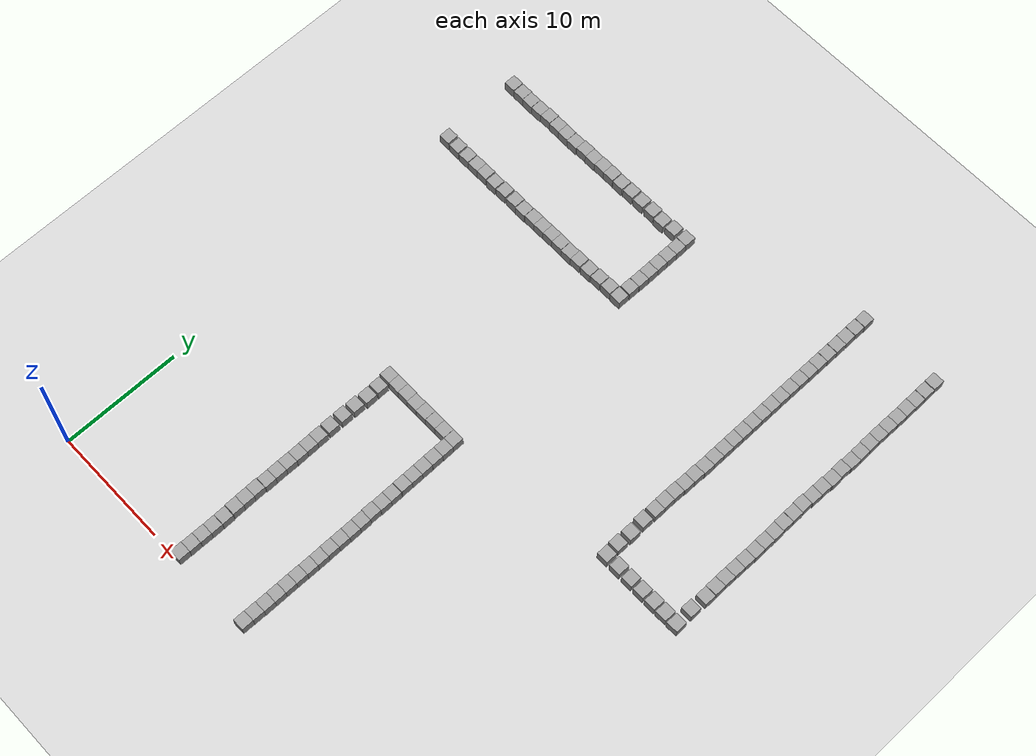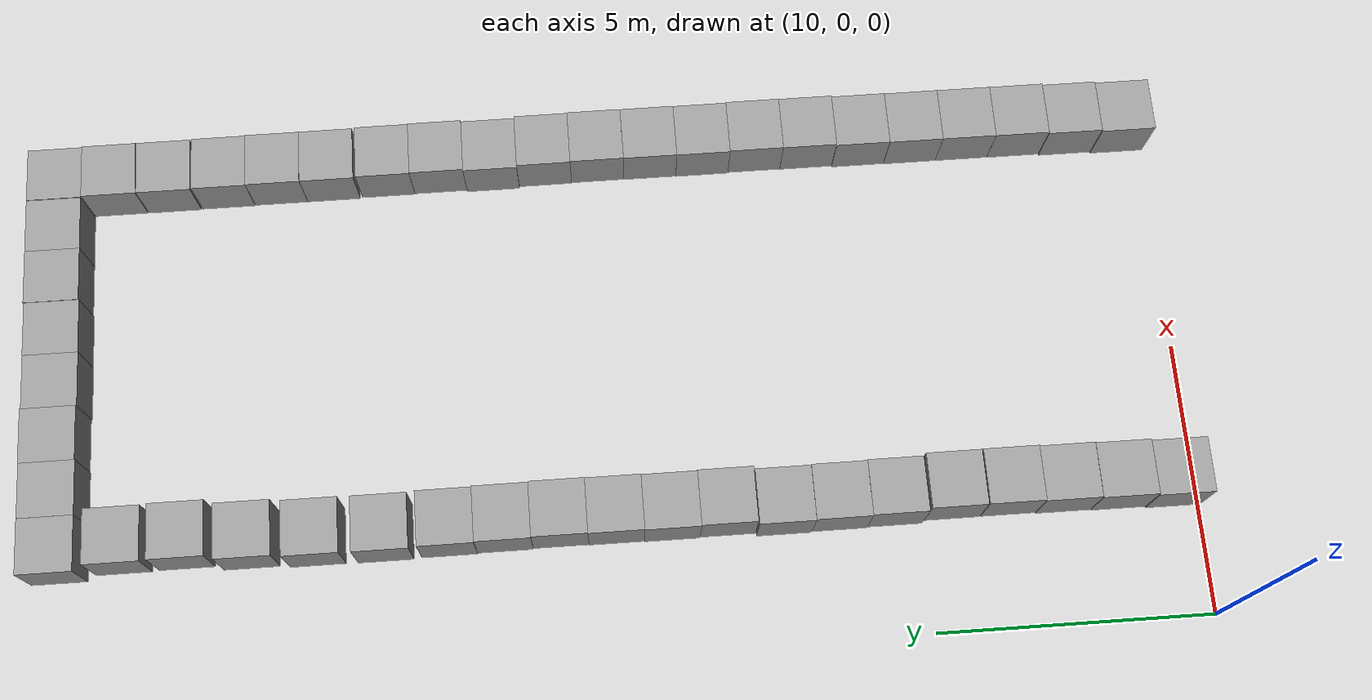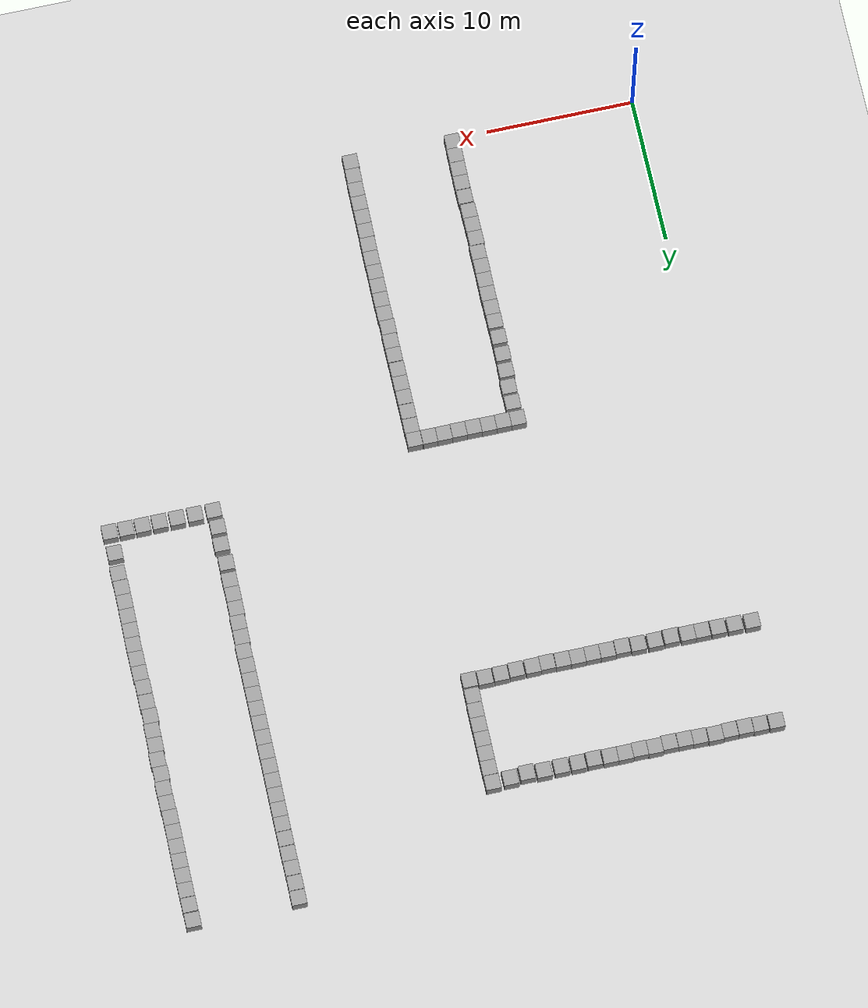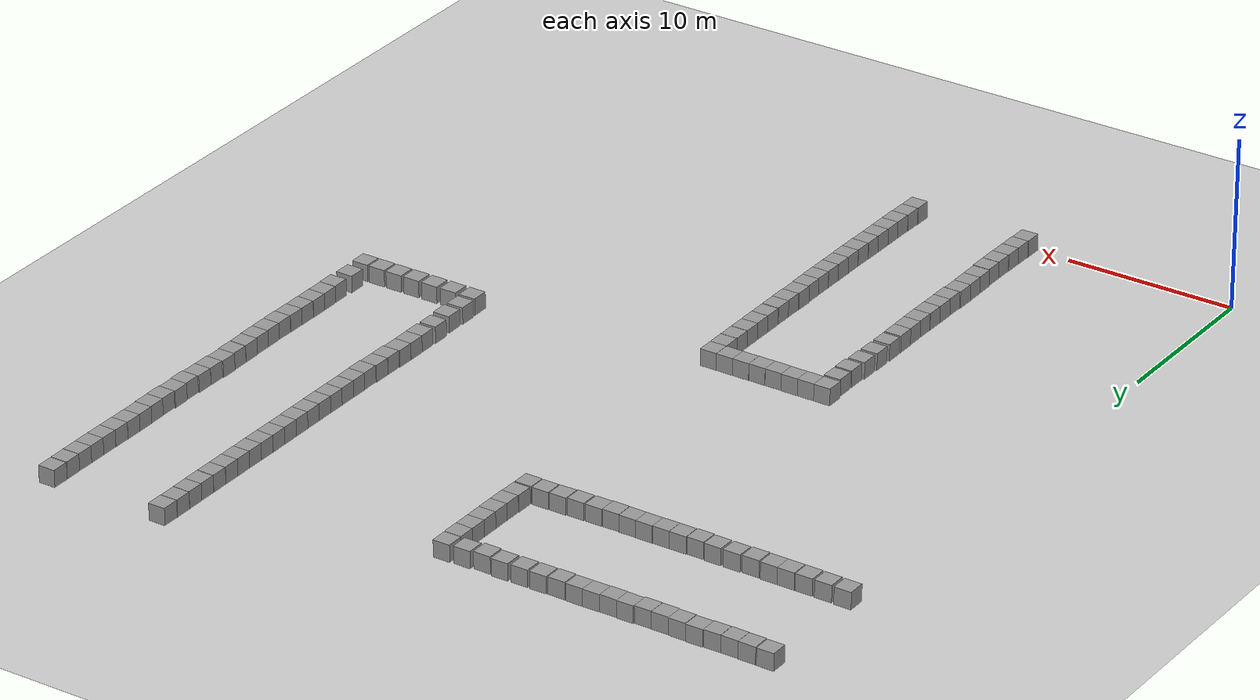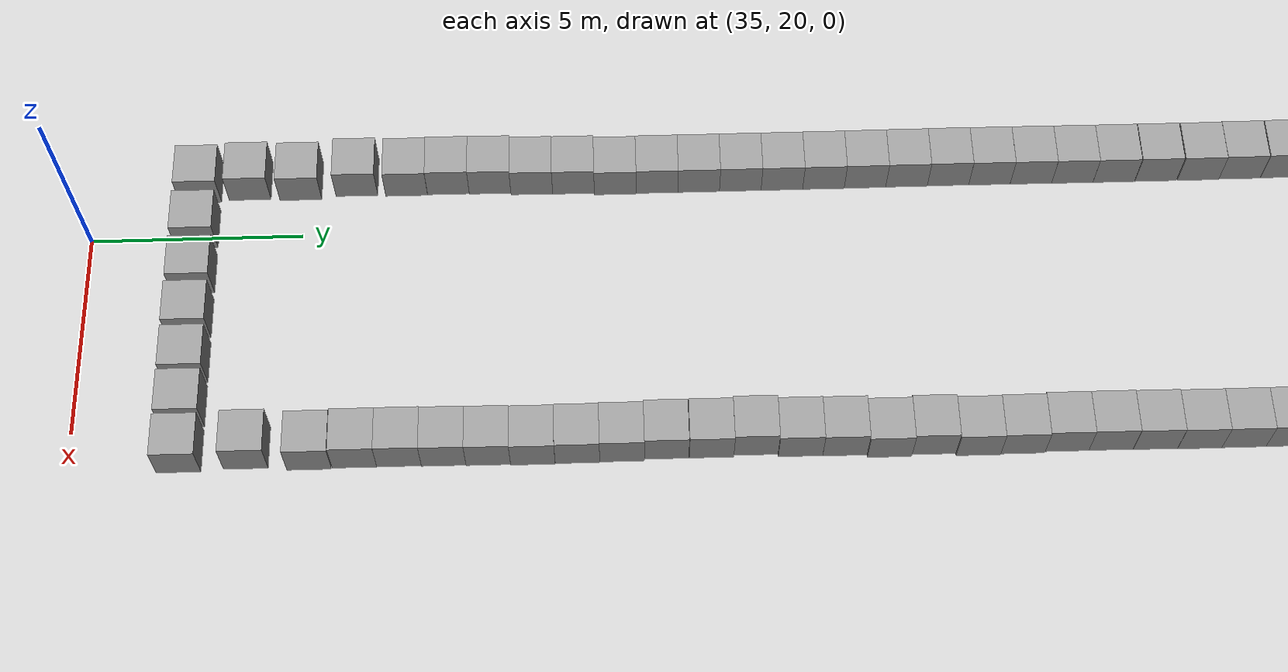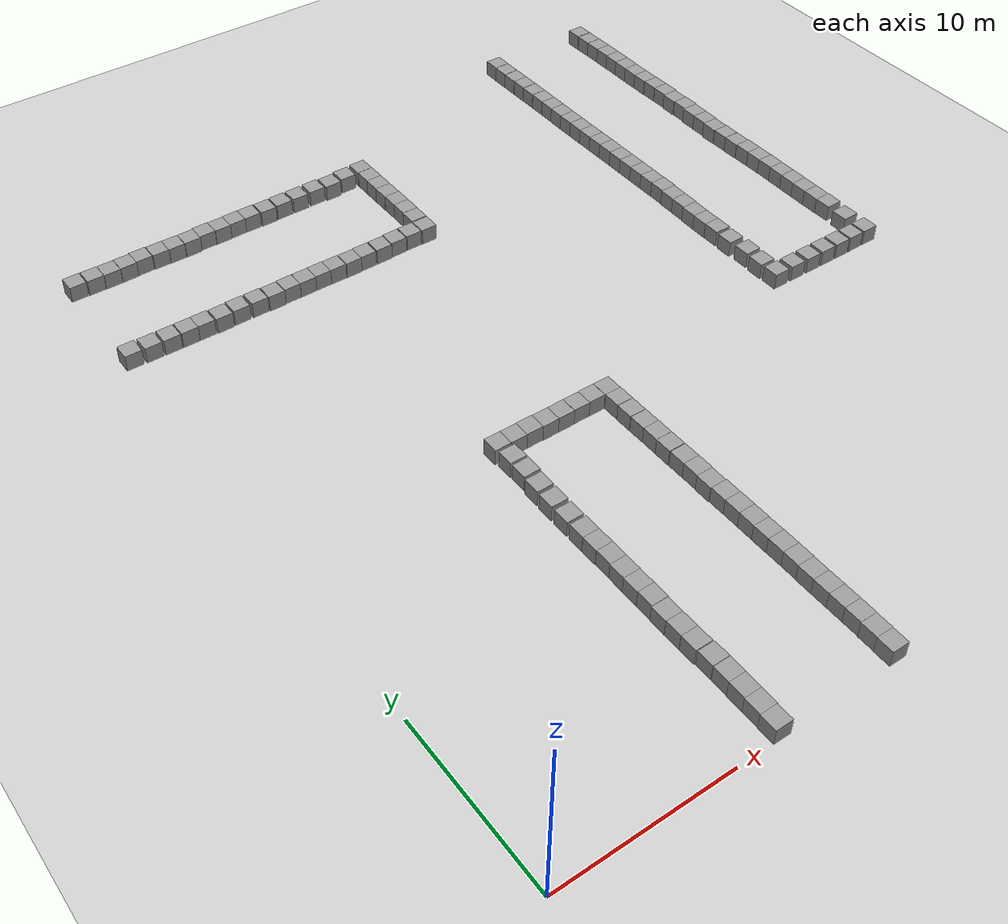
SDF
<sdf version="1.4">
 <world name="default">
  <light name="sun" type="directional">
   <pose>0 0 10 0 -0 0</pose>
   <diffuse>0.8 0.8 0.8 1</diffuse>
   <specular>0.2 0.2 0.2 1</specular>
   <attenuation>
    <range>1000</range>
    <constant>0.9</constant>
    <linear>0.01</linear>
    <quadratic>0.001</quadratic>
   </attenuation>
   <direction>-0.5 0.1 -0.9</direction>
  </light>
  <model name="ground_plane">
   <static>1</static>
   <link name="link">
    <collision name="collision">
     <geometry><plane><normal>0 0 1</normal><size>100 100</size></plane></geometry>
     <surface><friction><ode><mu>100</mu><mu2>50</mu2></ode></friction></surface>
    </collision>
    <visual name="visual">
     <cast_shadows>0</cast_shadows>
     <geometry><plane><normal>0 0 1</normal><size>100 100</size></plane></geometry>
     <material>
      <script><uri>file://media/materials/scripts/gazebo.material</uri><name>Gazebo/Grey</name></script>
     </material>
    </visual>
    <velocity_decay><linear>0</linear><angular>0</angular></velocity_decay>
   </link>
  </model>
  <physics type="ode">
   <max_step_size>0.001</max_step_size>
   <real_time_factor>1</real_time_factor>
   <real_time_update_rate>1000</real_time_update_rate>
   <gravity>0 0 -9.8</gravity>
  </physics>
  <scene><ambient>0.4 0.4 0.4 1</ambient><background>0.7 0.7 0.7 1</background><shadows>1</shadows></scene>
  <spherical_coordinates>
   <surface_model>EARTH_WGS84</surface_model>
   <latitude_deg>0</latitude_deg>
   <longitude_deg>0</longitude_deg>
   <elevation>0</elevation>
   <heading_deg>0</heading_deg>
  </spherical_coordinates>
  <model name="unit_box_1">
   <pose>15.2627 37.4478 0.5 0 0 -0.00037</pose>
   <link name="link">
    <inertial>
     <mass>1</mass>
     <inertia><ixx>1</ixx><ixy>0</ixy><ixz>0</ixz><iyy>1</iyy><iyz>0</iyz><izz>1</izz></inertia>
    </inertial>
    <collision name="collision"><geometry><box><size>1 1 1</size></box></geometry></collision>
    <visual name="visual">
     <geometry><box><size>1 1 1</size></box></geometry>
     <material>
      <script><uri>file://media/materials/scripts/gazebo.material</uri><name>Gazebo/Grey</name></script>
     </material>
    </visual>
    <velocity_decay><linear>0</linear><angular>0</angular></velocity_decay>
   </link>
   <static>0</static>
  </model>
  <model name="unit_box_2">
   <pose>12.5062 0.446914 0.5 0 0 -0.000451</pose>
   <link name="link">
    <inertial>
     <mass>1</mass>
     <inertia><ixx>1</ixx><ixy>0</ixy><ixz>0</ixz><iyy>1</iyy><iyz>0</iyz><izz>1</izz></inertia>
    </inertial>
    <collision name="collision"><geometry><box><size>1 1 1</size></box></geometry></collision>
    <visual name="visual">
     <geometry><box><size>1 1 1</size></box></geometry>
     <material>
      <script><uri>file://media/materials/scripts/gazebo.material</uri><name>Gazebo/Grey</name></script>
     </material>
    </visual>
    <velocity_decay><linear>0</linear><angular>0</angular></velocity_decay>
   </link>
   <static>0</static>
  </model>
  <model name="unit_box_3">
   <pose>19.5401 41.5958 0.5 0 -0 0.000629</pose>
   <link name="link">
    <inertial>
     <mass>1</mass>
     <inertia><ixx>1</ixx><ixy>0</ixy><ixz>0</ixz><iyy>1</iyy><iyz>0</iyz><izz>1</izz></inertia>
    </inertial>
    <collision name="collision"><geometry><box><size>1 1 1</size></box></geometry></collision>
    <visual name="visual">
     <geometry><box><size>1 1 1</size></box></geometry>
     <material>
      <script><uri>file://media/materials/scripts/gazebo.material</uri><name>Gazebo/Grey</name></script>
     </material>
    </visual>
    <velocity_decay><linear>0</linear><angular>0</angular></velocity_decay>
   </link>
   <static>0</static>
  </model>
  <model name="unit_box_4">
   <pose>19.5489 40.5957 0.5 -3.14159 -0 -3.141</pose>
   <link name="link">
    <inertial>
     <mass>1</mass>
     <inertia><ixx>1</ixx><ixy>0</ixy><ixz>0</ixz><iyy>1</iyy><iyz>0</iyz><izz>1</izz></inertia>
    </inertial>
    <collision name="collision"><geometry><box><size>1 1 1</size></box></geometry></collision>
    <visual name="visual">
     <geometry><box><size>1 1 1</size></box></geometry>
     <material>
      <script><uri>file://media/materials/scripts/gazebo.material</uri><name>Gazebo/Grey</name></script>
     </material>
    </visual>
    <velocity_decay><linear>0</linear><angular>0</angular></velocity_decay>
   </link>
   <static>0</static>
  </model>
  <model name="unit_box_5">
   <pose>19.5412 42.5958 0.5 0 -0 0.000513</pose>
   <link name="link">
    <inertial>
     <mass>1</mass>
     <inertia><ixx>1</ixx><ixy>0</ixy><ixz>0</ixz><iyy>1</iyy><iyz>0</iyz><izz>1</izz></inertia>
    </inertial>
    <collision name="collision"><geometry><box><size>1 1 1</size></box></geometry></collision>
    <visual name="visual">
     <geometry><box><size>1 1 1</size></box></geometry>
     <material>
      <script><uri>file://media/materials/scripts/gazebo.material</uri><name>Gazebo/Grey</name></script>
     </material>
    </visual>
    <velocity_decay><linear>0</linear><angular>0</angular></velocity_decay>
   </link>
   <static>0</static>
  </model>
  <model name="unit_box_6">
   <pose>8.15665 37.4382 0.5 0 -0 0</pose>
   <link name="link">
    <inertial>
     <mass>1</mass>
     <inertia><ixx>1</ixx><ixy>0</ixy><ixz>0</ixz><iyy>1</iyy><iyz>0</iyz><izz>1</izz></inertia>
    </inertial>
    <collision name="collision"><geometry><box><size>1 1 1</size></box></geometry></collision>
    <visual name="visual">
     <geometry><box><size>1 1 1</size></box></geometry>
     <material>
      <script><uri>file://media/materials/scripts/gazebo.material</uri><name>Gazebo/Grey</name></script>
     </material>
    </visual>
    <velocity_decay><linear>0</linear><angular>0</angular></velocity_decay>
   </link>
   <static>0</static>
  </model>
  <model name="unit_box_7">
   <pose>17.3937 37.5116 0.5 0 -0 -0.000796</pose>
   <link name="link">
    <inertial>
     <mass>1</mass>
     <inertia><ixx>1</ixx><ixy>0</ixy><ixz>0</ixz><iyy>1</iyy><iyz>0</iyz><izz>1</izz></inertia>
    </inertial>
    <collision name="collision"><geometry><box><size>1 1 1</size></box></geometry></collision>
    <visual name="visual">
     <geometry><box><size>1 1 1</size></box></geometry>
     <material>
      <script><uri>file://media/materials/scripts/gazebo.material</uri><name>Gazebo/Grey</name></script>
     </material>
    </visual>
    <velocity_decay><linear>0</linear><angular>0</angular></velocity_decay>
   </link>
   <static>0</static>
  </model>
  <model name="unit_box_8">
   <pose>7.02469 37.4425 0.5 0 -0 4.7e-05</pose>
   <link name="link">
    <inertial>
     <mass>1</mass>
     <inertia><ixx>1</ixx><ixy>0</ixy><ixz>0</ixz><iyy>1</iyy><iyz>0</iyz><izz>1</izz></inertia>
    </inertial>
    <collision name="collision"><geometry><box><size>1 1 1</size></box></geometry></collision>
    <visual name="visual">
     <geometry><box><size>1 1 1</size></box></geometry>
     <material>
      <script><uri>file://media/materials/scripts/gazebo.material</uri><name>Gazebo/Grey</name></script>
     </material>
    </visual>
    <velocity_decay><linear>0</linear><angular>0</angular></velocity_decay>
   </link>
   <static>0</static>
  </model>
  <model name="unit_box_9">
   <pose>16.3457 37.4558 0.5 0 0 -0.000796</pose>
   <link name="link">
    <inertial>
     <mass>1</mass>
     <inertia><ixx>1</ixx><ixy>0</ixy><ixz>0</ixz><iyy>1</iyy><iyz>0</iyz><izz>1</izz></inertia>
    </inertial>
    <collision name="collision"><geometry><box><size>1 1 1</size></box></geometry></collision>
    <visual name="visual">
     <geometry><box><size>1 1 1</size></box></geometry>
     <material>
      <script><uri>file://media/materials/scripts/gazebo.material</uri><name>Gazebo/Grey</name></script>
     </material>
    </visual>
    <velocity_decay><linear>0</linear><angular>0</angular></velocity_decay>
   </link>
   <static>0</static>
  </model>
  <model name="unit_box_10">
   <pose>5.93209 37.3997 0.5 0 0 -0.000146</pose>
   <link name="link">
    <inertial>
     <mass>1</mass>
     <inertia><ixx>1</ixx><ixy>0</ixy><ixz>0</ixz><iyy>1</iyy><iyz>0</iyz><izz>1</izz></inertia>
    </inertial>
    <collision name="collision"><geometry><box><size>1 1 1</size></box></geometry></collision>
    <visual name="visual">
     <geometry><box><size>1 1 1</size></box></geometry>
     <material>
      <script><uri>file://media/materials/scripts/gazebo.material</uri><name>Gazebo/Grey</name></script>
     </material>
    </visual>
    <velocity_decay><linear>0</linear><angular>0</angular></velocity_decay>
   </link>
   <static>0</static>
  </model>
  <model name="unit_box_11">
   <pose>2.78254 37.4481 0.5 -0 -0 -0.000206</pose>
   <link name="link">
    <inertial>
     <mass>1</mass>
     <inertia><ixx>1</ixx><ixy>0</ixy><ixz>0</ixz><iyy>1</iyy><iyz>0</iyz><izz>1</izz></inertia>
    </inertial>
    <collision name="collision"><geometry><box><size>1 1 1</size></box></geometry></collision>
    <visual name="visual">
     <geometry><box><size>1 1 1</size></box></geometry>
     <material>
      <script><uri>file://media/materials/scripts/gazebo.material</uri><name>Gazebo/Grey</name></script>
     </material>
    </visual>
    <velocity_decay><linear>0</linear><angular>0</angular></velocity_decay>
   </link>
   <static>0</static>
  </model>
  <model name="unit_box_12">
   <pose>1.66601 37.4668 0.5 0 0 -0.000206</pose>
   <link name="link">
    <inertial>
     <mass>1</mass>
     <inertia><ixx>1</ixx><ixy>0</ixy><ixz>0</ixz><iyy>1</iyy><iyz>0</iyz><izz>1</izz></inertia>
    </inertial>
    <collision name="collision"><geometry><box><size>1 1 1</size></box></geometry></collision>
    <visual name="visual">
     <geometry><box><size>1 1 1</size></box></geometry>
     <material>
      <script><uri>file://media/materials/scripts/gazebo.material</uri><name>Gazebo/Grey</name></script>
     </material>
    </visual>
    <velocity_decay><linear>0</linear><angular>0</angular></velocity_decay>
   </link>
   <static>0</static>
  </model>
  <model name="unit_box_13">
   <pose>4.83791 37.4433 0.5 0 0 -0.000272</pose>
   <link name="link">
    <inertial>
     <mass>1</mass>
     <inertia><ixx>1</ixx><ixy>0</ixy><ixz>0</ixz><iyy>1</iyy><iyz>0</iyz><izz>1</izz></inertia>
    </inertial>
    <collision name="collision"><geometry><box><size>1 1 1</size></box></geometry></collision>
    <visual name="visual">
     <geometry><box><size>1 1 1</size></box></geometry>
     <material>
      <script><uri>file://media/materials/scripts/gazebo.material</uri><name>Gazebo/Grey</name></script>
     </material>
    </visual>
    <velocity_decay><linear>0</linear><angular>0</angular></velocity_decay>
   </link>
   <static>0</static>
  </model>
  <model name="unit_box_14">
   <pose>3.83791 37.445 0.5 0 -0 -0.000273</pose>
   <link name="link">
    <inertial>
     <mass>1</mass>
     <inertia><ixx>1</ixx><ixy>0</ixy><ixz>0</ixz><iyy>1</iyy><iyz>0</iyz><izz>1</izz></inertia>
    </inertial>
    <collision name="collision"><geometry><box><size>1 1 1</size></box></geometry></collision>
    <visual name="visual">
     <geometry><box><size>1 1 1</size></box></geometry>
     <material>
      <script><uri>file://media/materials/scripts/gazebo.material</uri><name>Gazebo/Grey</name></script>
     </material>
    </visual>
    <velocity_decay><linear>0</linear><angular>0</angular></velocity_decay>
   </link>
   <static>0</static>
  </model>
  <model name="unit_box_15">
   <pose>19.546 39.5957 0.5 0 -0 0.000517</pose>
   <link name="link">
    <inertial>
     <mass>1</mass>
     <inertia><ixx>1</ixx><ixy>0</ixy><ixz>0</ixz><iyy>1</iyy><iyz>0</iyz><izz>1</izz></inertia>
    </inertial>
    <collision name="collision"><geometry><box><size>1 1 1</size></box></geometry></collision>
    <visual name="visual">
     <geometry><box><size>1 1 1</size></box></geometry>
     <material>
      <script><uri>file://media/materials/scripts/gazebo.material</uri><name>Gazebo/Grey</name></script>
     </material>
    </visual>
    <velocity_decay><linear>0</linear><angular>0</angular></velocity_decay>
   </link>
   <static>0</static>
  </model>
  <model name="unit_box_16">
   <pose>19.5222 38.589 0.5 0 0 -0.000568</pose>
   <link name="link">
    <inertial>
     <mass>1</mass>
     <inertia><ixx>1</ixx><ixy>0</ixy><ixz>0</ixz><iyy>1</iyy><iyz>0</iyz><izz>1</izz></inertia>
    </inertial>
    <collision name="collision"><geometry><box><size>1 1 1</size></box></geometry></collision>
    <visual name="visual">
     <geometry><box><size>1 1 1</size></box></geometry>
     <material>
      <script><uri>file://media/materials/scripts/gazebo.material</uri><name>Gazebo/Grey</name></script>
     </material>
    </visual>
    <velocity_decay><linear>0</linear><angular>0</angular></velocity_decay>
   </link>
   <static>0</static>
  </model>
  <model name="unit_box_17">
   <pose>19.5451 43.5958 0.5 0 -0 0.000513</pose>
   <link name="link">
    <inertial>
     <mass>1</mass>
     <inertia><ixx>1</ixx><ixy>0</ixy><ixz>0</ixz><iyy>1</iyy><iyz>0</iyz><izz>1</izz></inertia>
    </inertial>
    <collision name="collision"><geometry><box><size>1 1 1</size></box></geometry></collision>
    <visual name="visual">
     <geometry><box><size>1 1 1</size></box></geometry>
     <material>
      <script><uri>file://media/materials/scripts/gazebo.material</uri><name>Gazebo/Grey</name></script>
     </material>
    </visual>
    <velocity_decay><linear>0</linear><angular>0</angular></velocity_decay>
   </link>
   <static>0</static>
  </model>
  <model name="unit_box_18">
   <pose>14.2627 37.4121 0.5 0 -0 -0.00037</pose>
   <link name="link">
    <inertial>
     <mass>1</mass>
     <inertia><ixx>1</ixx><ixy>0</ixy><ixz>0</ixz><iyy>1</iyy><iyz>0</iyz><izz>1</izz></inertia>
    </inertial>
    <collision name="collision"><geometry><box><size>1 1 1</size></box></geometry></collision>
    <visual name="visual">
     <geometry><box><size>1 1 1</size></box></geometry>
     <material>
      <script><uri>file://media/materials/scripts/gazebo.material</uri><name>Gazebo/Grey</name></script>
     </material>
    </visual>
    <velocity_decay><linear>0</linear><angular>0</angular></velocity_decay>
   </link>
   <static>0</static>
  </model>
  <model name="unit_box_19">
   <pose>13.2384 37.4353 0.5 0 0 -0.000791</pose>
   <link name="link">
    <inertial>
     <mass>1</mass>
     <inertia><ixx>1</ixx><ixy>0</ixy><ixz>0</ixz><iyy>1</iyy><iyz>0</iyz><izz>1</izz></inertia>
    </inertial>
    <collision name="collision"><geometry><box><size>1 1 1</size></box></geometry></collision>
    <visual name="visual">
     <geometry><box><size>1 1 1</size></box></geometry>
     <material>
      <script><uri>file://media/materials/scripts/gazebo.material</uri><name>Gazebo/Grey</name></script>
     </material>
    </visual>
    <velocity_decay><linear>0</linear><angular>0</angular></velocity_decay>
   </link>
   <static>0</static>
  </model>
  <model name="unit_box_20">
   <pose>12.2385 37.4461 0.5 0 0 -0.000786</pose>
   <link name="link">
    <inertial>
     <mass>1</mass>
     <inertia><ixx>1</ixx><ixy>0</ixy><ixz>0</ixz><iyy>1</iyy><iyz>0</iyz><izz>1</izz></inertia>
    </inertial>
    <collision name="collision"><geometry><box><size>1 1 1</size></box></geometry></collision>
    <visual name="visual">
     <geometry><box><size>1 1 1</size></box></geometry>
     <material>
      <script><uri>file://media/materials/scripts/gazebo.material</uri><name>Gazebo/Grey</name></script>
     </material>
    </visual>
    <velocity_decay><linear>0</linear><angular>0</angular></velocity_decay>
   </link>
   <static>0</static>
  </model>
  <model name="unit_box_21">
   <pose>11.2383 37.4328 0.5 0 0 -0.000588</pose>
   <link name="link">
    <inertial>
     <mass>1</mass>
     <inertia><ixx>1</ixx><ixy>0</ixy><ixz>0</ixz><iyy>1</iyy><iyz>0</iyz><izz>1</izz></inertia>
    </inertial>
    <collision name="collision"><geometry><box><size>1 1 1</size></box></geometry></collision>
    <visual name="visual">
     <geometry><box><size>1 1 1</size></box></geometry>
     <material>
      <script><uri>file://media/materials/scripts/gazebo.material</uri><name>Gazebo/Grey</name></script>
     </material>
    </visual>
    <velocity_decay><linear>0</linear><angular>0</angular></velocity_decay>
   </link>
   <static>0</static>
  </model>
  <model name="unit_box_22">
   <pose>10.2343 37.4366 0.5 0 0 -0.000547</pose>
   <link name="link">
    <inertial>
     <mass>1</mass>
     <inertia><ixx>1</ixx><ixy>0</ixy><ixz>0</ixz><iyy>1</iyy><iyz>0</iyz><izz>1</izz></inertia>
    </inertial>
    <collision name="collision"><geometry><box><size>1 1 1</size></box></geometry></collision>
    <visual name="visual">
     <geometry><box><size>1 1 1</size></box></geometry>
     <material>
      <script><uri>file://media/materials/scripts/gazebo.material</uri><name>Gazebo/Grey</name></script>
     </material>
    </visual>
    <velocity_decay><linear>0</linear><angular>0</angular></velocity_decay>
   </link>
   <static>0</static>
  </model>
  <model name="unit_box_23">
   <pose>18.4531 37.5349 0.5 0 0 -0.000568</pose>
   <link name="link">
    <inertial>
     <mass>1</mass>
     <inertia><ixx>1</ixx><ixy>0</ixy><ixz>0</ixz><iyy>1</iyy><iyz>0</iyz><izz>1</izz></inertia>
    </inertial>
    <collision name="collision"><geometry><box><size>1 1 1</size></box></geometry></collision>
    <visual name="visual">
     <geometry><box><size>1 1 1</size></box></geometry>
     <material>
      <script><uri>file://media/materials/scripts/gazebo.material</uri><name>Gazebo/Grey</name></script>
     </material>
    </visual>
    <velocity_decay><linear>0</linear><angular>0</angular></velocity_decay>
   </link>
   <static>0</static>
  </model>
  <model name="unit_box_25">
   <pose>9.20921 37.3925 0.5 0 -0 -0.000667</pose>
   <link name="link">
    <inertial>
     <mass>1</mass>
     <inertia><ixx>1</ixx><ixy>0</ixy><ixz>0</ixz><iyy>1</iyy><iyz>0</iyz><izz>1</izz></inertia>
    </inertial>
    <collision name="collision"><geometry><box><size>1 1 1</size></box></geometry></collision>
    <visual name="visual">
     <geometry><box><size>1 1 1</size></box></geometry>
     <material>
      <script><uri>file://media/materials/scripts/gazebo.material</uri><name>Gazebo/Grey</name></script>
     </material>
    </visual>
    <velocity_decay><linear>0</linear><angular>0</angular></velocity_decay>
   </link>
   <static>0</static>
  </model>
  <model name="unit_box_26">
   <pose>19.5048 37.5063 0.5 0 -0 -0.000667</pose>
   <link name="link">
    <inertial>
     <mass>1</mass>
     <inertia><ixx>1</ixx><ixy>0</ixy><ixz>0</ixz><iyy>1</iyy><iyz>0</iyz><izz>1</izz></inertia>
    </inertial>
    <collision name="collision"><geometry><box><size>1 1 1</size></box></geometry></collision>
    <visual name="visual">
     <geometry><box><size>1 1 1</size></box></geometry>
     <material>
      <script><uri>file://media/materials/scripts/gazebo.material</uri><name>Gazebo/Grey</name></script>
     </material>
    </visual>
    <velocity_decay><linear>0</linear><angular>0</angular></velocity_decay>
   </link>
   <static>0</static>
  </model>
  <model name="unit_box_27">
   <pose>12.4867 20.4985 0.5 0 -0 0.000241</pose>
   <link name="link">
    <inertial>
     <mass>1</mass>
     <inertia><ixx>1</ixx><ixy>0</ixy><ixz>0</ixz><iyy>1</iyy><iyz>0</iyz><izz>1</izz></inertia>
    </inertial>
    <collision name="collision"><geometry><box><size>1 1 1</size></box></geometry></collision>
    <visual name="visual">
     <geometry><box><size>1 1 1</size></box></geometry>
     <material>
      <script><uri>file://media/materials/scripts/gazebo.material</uri><name>Gazebo/Grey</name></script>
     </material>
    </visual>
    <velocity_decay><linear>0</linear><angular>0</angular></velocity_decay>
   </link>
   <static>0</static>
  </model>
  <model name="unit_box_28">
   <pose>19.4998 0.427452 0.5 0 0 -6.1e-05</pose>
   <link name="link">
    <inertial>
     <mass>1</mass>
     <inertia><ixx>1</ixx><ixy>0</ixy><ixz>0</ixz><iyy>1</iyy><iyz>0</iyz><izz>1</izz></inertia>
    </inertial>
    <collision name="collision"><geometry><box><size>1 1 1</size></box></geometry></collision>
    <visual name="visual">
     <geometry><box><size>1 1 1</size></box></geometry>
     <material>
      <script><uri>file://media/materials/scripts/gazebo.material</uri><name>Gazebo/Grey</name></script>
     </material>
    </visual>
    <velocity_decay><linear>0</linear><angular>0</angular></velocity_decay>
   </link>
   <static>0</static>
  </model>
  <model name="unit_box_29">
   <pose>19.5022 20.5077 0.5 0 -0 2.5e-05</pose>
   <link name="link">
    <inertial>
     <mass>1</mass>
     <inertia><ixx>1</ixx><ixy>0</ixy><ixz>0</ixz><iyy>1</iyy><iyz>0</iyz><izz>1</izz></inertia>
    </inertial>
    <collision name="collision"><geometry><box><size>1 1 1</size></box></geometry></collision>
    <visual name="visual">
     <geometry><box><size>1 1 1</size></box></geometry>
     <material>
      <script><uri>file://media/materials/scripts/gazebo.material</uri><name>Gazebo/Grey</name></script>
     </material>
    </visual>
    <velocity_decay><linear>0</linear><angular>0</angular></velocity_decay>
   </link>
   <static>0</static>
  </model>
  <model name="unit_box_30">
   <pose>12.5309 1.44691 0.5 0 0 -0.00045</pose>
   <link name="link">
    <inertial>
     <mass>1</mass>
     <inertia><ixx>1</ixx><ixy>0</ixy><ixz>0</ixz><iyy>1</iyy><iyz>0</iyz><izz>1</izz></inertia>
    </inertial>
    <collision name="collision"><geometry><box><size>1 1 1</size></box></geometry></collision>
    <visual name="visual">
     <geometry><box><size>1 1 1</size></box></geometry>
     <material>
      <script><uri>file://media/materials/scripts/gazebo.material</uri><name>Gazebo/Grey</name></script>
     </material>
    </visual>
    <velocity_decay><linear>0</linear><angular>0</angular></velocity_decay>
   </link>
   <static>0</static>
  </model>
  <model name="unit_box_31">
   <pose>12.543 2.44871 0.5 0 -0 8e-06</pose>
   <link name="link">
    <inertial>
     <mass>1</mass>
     <inertia><ixx>1</ixx><ixy>0</ixy><ixz>0</ixz><iyy>1</iyy><iyz>0</iyz><izz>1</izz></inertia>
    </inertial>
    <collision name="collision"><geometry><box><size>1 1 1</size></box></geometry></collision>
    <visual name="visual">
     <geometry><box><size>1 1 1</size></box></geometry>
     <material>
      <script><uri>file://media/materials/scripts/gazebo.material</uri><name>Gazebo/Grey</name></script>
     </material>
    </visual>
    <velocity_decay><linear>0</linear><angular>0</angular></velocity_decay>
   </link>
   <static>0</static>
  </model>
  <model name="unit_box_32">
   <pose>12.5574 3.44871 0.5 0 -0 5e-06</pose>
   <link name="link">
    <inertial>
     <mass>1</mass>
     <inertia><ixx>1</ixx><ixy>0</ixy><ixz>0</ixz><iyy>1</iyy><iyz>0</iyz><izz>1</izz></inertia>
    </inertial>
    <collision name="collision"><geometry><box><size>1 1 1</size></box></geometry></collision>
    <visual name="visual">
     <geometry><box><size>1 1 1</size></box></geometry>
     <material>
      <script><uri>file://media/materials/scripts/gazebo.material</uri><name>Gazebo/Grey</name></script>
     </material>
    </visual>
    <velocity_decay><linear>0</linear><angular>0</angular></velocity_decay>
   </link>
   <static>0</static>
  </model>
  <model name="unit_box_33">
   <pose>12.5538 4.46862 0.5 0 -0 6e-06</pose>
   <link name="link">
    <inertial>
     <mass>1</mass>
     <inertia><ixx>1</ixx><ixy>0</ixy><ixz>0</ixz><iyy>1</iyy><iyz>0</iyz><izz>1</izz></inertia>
    </inertial>
    <collision name="collision"><geometry><box><size>1 1 1</size></box></geometry></collision>
    <visual name="visual">
     <geometry><box><size>1 1 1</size></box></geometry>
     <material>
      <script><uri>file://media/materials/scripts/gazebo.material</uri><name>Gazebo/Grey</name></script>
     </material>
    </visual>
    <velocity_decay><linear>0</linear><angular>0</angular></velocity_decay>
   </link>
   <static>0</static>
  </model>
  <model name="unit_box_34">
   <pose>12.5053 5.51432 0.5 0 -0 0.000187</pose>
   <link name="link">
    <inertial>
     <mass>1</mass>
     <inertia><ixx>1</ixx><ixy>0</ixy><ixz>0</ixz><iyy>1</iyy><iyz>0</iyz><izz>1</izz></inertia>
    </inertial>
    <collision name="collision"><geometry><box><size>1 1 1</size></box></geometry></collision>
    <visual name="visual">
     <geometry><box><size>1 1 1</size></box></geometry>
     <material>
      <script><uri>file://media/materials/scripts/gazebo.material</uri><name>Gazebo/Grey</name></script>
     </material>
    </visual>
    <velocity_decay><linear>0</linear><angular>0</angular></velocity_decay>
   </link>
   <static>0</static>
  </model>
  <model name="unit_box_35">
   <pose>12.4918 6.51502 0.5 0 -0 0.00017</pose>
   <link name="link">
    <inertial>
     <mass>1</mass>
     <inertia><ixx>1</ixx><ixy>0</ixy><ixz>0</ixz><iyy>1</iyy><iyz>0</iyz><izz>1</izz></inertia>
    </inertial>
    <collision name="collision"><geometry><box><size>1 1 1</size></box></geometry></collision>
    <visual name="visual">
     <geometry><box><size>1 1 1</size></box></geometry>
     <material>
      <script><uri>file://media/materials/scripts/gazebo.material</uri><name>Gazebo/Grey</name></script>
     </material>
    </visual>
    <velocity_decay><linear>0</linear><angular>0</angular></velocity_decay>
   </link>
   <static>0</static>
  </model>
  <model name="unit_box_36">
   <pose>12.4784 7.5163 0.5 0 -0 7.4e-05</pose>
   <link name="link">
    <inertial>
     <mass>1</mass>
     <inertia><ixx>1</ixx><ixy>0</ixy><ixz>0</ixz><iyy>1</iyy><iyz>0</iyz><izz>1</izz></inertia>
    </inertial>
    <collision name="collision"><geometry><box><size>1 1 1</size></box></geometry></collision>
    <visual name="visual">
     <geometry><box><size>1 1 1</size></box></geometry>
     <material>
      <script><uri>file://media/materials/scripts/gazebo.material</uri><name>Gazebo/Grey</name></script>
     </material>
    </visual>
    <velocity_decay><linear>0</linear><angular>0</angular></velocity_decay>
   </link>
   <static>0</static>
  </model>
  <model name="unit_box_37">
   <pose>12.5302 8.53127 0.5 0 -0 0.000439</pose>
   <link name="link">
    <inertial>
     <mass>1</mass>
     <inertia><ixx>1</ixx><ixy>0</ixy><ixz>0</ixz><iyy>1</iyy><iyz>0</iyz><izz>1</izz></inertia>
    </inertial>
    <collision name="collision"><geometry><box><size>1 1 1</size></box></geometry></collision>
    <visual name="visual">
     <geometry><box><size>1 1 1</size></box></geometry>
     <material>
      <script><uri>file://media/materials/scripts/gazebo.material</uri><name>Gazebo/Grey</name></script>
     </material>
    </visual>
    <velocity_decay><linear>0</linear><angular>0</angular></velocity_decay>
   </link>
   <static>0</static>
  </model>
  <model name="unit_box_38">
   <pose>12.5171 9.53128 0.5 0 -0 0.000436</pose>
   <link name="link">
    <inertial>
     <mass>1</mass>
     <inertia><ixx>1</ixx><ixy>0</ixy><ixz>0</ixz><iyy>1</iyy><iyz>0</iyz><izz>1</izz></inertia>
    </inertial>
    <collision name="collision"><geometry><box><size>1 1 1</size></box></geometry></collision>
    <visual name="visual">
     <geometry><box><size>1 1 1</size></box></geometry>
     <material>
      <script><uri>file://media/materials/scripts/gazebo.material</uri><name>Gazebo/Grey</name></script>
     </material>
    </visual>
    <velocity_decay><linear>0</linear><angular>0</angular></velocity_decay>
   </link>
   <static>0</static>
  </model>
  <model name="unit_box_39">
   <pose>12.5257 10.5313 0.5 0 -0 0.000397</pose>
   <link name="link">
    <inertial>
     <mass>1</mass>
     <inertia><ixx>1</ixx><ixy>0</ixy><ixz>0</ixz><iyy>1</iyy><iyz>0</iyz><izz>1</izz></inertia>
    </inertial>
    <collision name="collision"><geometry><box><size>1 1 1</size></box></geometry></collision>
    <visual name="visual">
     <geometry><box><size>1 1 1</size></box></geometry>
     <material>
      <script><uri>file://media/materials/scripts/gazebo.material</uri><name>Gazebo/Grey</name></script>
     </material>
    </visual>
    <velocity_decay><linear>0</linear><angular>0</angular></velocity_decay>
   </link>
   <static>0</static>
  </model>
  <model name="unit_box_40">
   <pose>12.5333 11.5313 0.5 0 -0 0.000398</pose>
   <link name="link">
    <inertial>
     <mass>1</mass>
     <inertia><ixx>1</ixx><ixy>0</ixy><ixz>0</ixz><iyy>1</iyy><iyz>0</iyz><izz>1</izz></inertia>
    </inertial>
    <collision name="collision"><geometry><box><size>1 1 1</size></box></geometry></collision>
    <visual name="visual">
     <geometry><box><size>1 1 1</size></box></geometry>
     <material>
      <script><uri>file://media/materials/scripts/gazebo.material</uri><name>Gazebo/Grey</name></script>
     </material>
    </visual>
    <velocity_decay><linear>0</linear><angular>0</angular></velocity_decay>
   </link>
   <static>0</static>
  </model>
  <model name="unit_box_41">
   <pose>12.5184 12.5313 0.5 0 -0 0.000369</pose>
   <link name="link">
    <inertial>
     <mass>1</mass>
     <inertia><ixx>1</ixx><ixy>0</ixy><ixz>0</ixz><iyy>1</iyy><iyz>0</iyz><izz>1</izz></inertia>
    </inertial>
    <collision name="collision"><geometry><box><size>1 1 1</size></box></geometry></collision>
    <visual name="visual">
     <geometry><box><size>1 1 1</size></box></geometry>
     <material>
      <script><uri>file://media/materials/scripts/gazebo.material</uri><name>Gazebo/Grey</name></script>
     </material>
    </visual>
    <velocity_decay><linear>0</linear><angular>0</angular></velocity_decay>
   </link>
   <static>0</static>
  </model>
  <model name="unit_box_42">
   <pose>12.5039 13.5313 0.5 0 -0 0.000354</pose>
   <link name="link">
    <inertial>
     <mass>1</mass>
     <inertia><ixx>1</ixx><ixy>0</ixy><ixz>0</ixz><iyy>1</iyy><iyz>0</iyz><izz>1</izz></inertia>
    </inertial>
    <collision name="collision"><geometry><box><size>1 1 1</size></box></geometry></collision>
    <visual name="visual">
     <geometry><box><size>1 1 1</size></box></geometry>
     <material>
      <script><uri>file://media/materials/scripts/gazebo.material</uri><name>Gazebo/Grey</name></script>
     </material>
    </visual>
    <velocity_decay><linear>0</linear><angular>0</angular></velocity_decay>
   </link>
   <static>0</static>
  </model>
  <model name="unit_box_43">
   <pose>12.488 14.6714 0.5 0 -0 0.000276</pose>
   <link name="link">
    <inertial>
     <mass>1</mass>
     <inertia><ixx>1</ixx><ixy>0</ixy><ixz>0</ixz><iyy>1</iyy><iyz>0</iyz><izz>1</izz></inertia>
    </inertial>
    <collision name="collision"><geometry><box><size>1 1 1</size></box></geometry></collision>
    <visual name="visual">
     <geometry><box><size>1 1 1</size></box></geometry>
     <material>
      <script><uri>file://media/materials/scripts/gazebo.material</uri><name>Gazebo/Grey</name></script>
     </material>
    </visual>
    <velocity_decay><linear>0</linear><angular>0</angular></velocity_decay>
   </link>
   <static>0</static>
  </model>
  <model name="unit_box_44">
   <pose>12.4951 15.89 0.5 0 -0 0.000272</pose>
   <link name="link">
    <inertial>
     <mass>1</mass>
     <inertia><ixx>1</ixx><ixy>0</ixy><ixz>0</ixz><iyy>1</iyy><iyz>0</iyz><izz>1</izz></inertia>
    </inertial>
    <collision name="collision"><geometry><box><size>1 1 1</size></box></geometry></collision>
    <visual name="visual">
     <geometry><box><size>1 1 1</size></box></geometry>
     <material>
      <script><uri>file://media/materials/scripts/gazebo.material</uri><name>Gazebo/Grey</name></script>
     </material>
    </visual>
    <velocity_decay><linear>0</linear><angular>0</angular></velocity_decay>
   </link>
   <static>0</static>
  </model>
  <model name="unit_box_45">
   <pose>12.5264 17.0697 0.5 0 -0 0.000256</pose>
   <link name="link">
    <inertial>
     <mass>1</mass>
     <inertia><ixx>1</ixx><ixy>0</ixy><ixz>0</ixz><iyy>1</iyy><iyz>0</iyz><izz>1</izz></inertia>
    </inertial>
    <collision name="collision"><geometry><box><size>1 1 1</size></box></geometry></collision>
    <visual name="visual">
     <geometry><box><size>1 1 1</size></box></geometry>
     <material>
      <script><uri>file://media/materials/scripts/gazebo.material</uri><name>Gazebo/Grey</name></script>
     </material>
    </visual>
    <velocity_decay><linear>0</linear><angular>0</angular></velocity_decay>
   </link>
   <static>0</static>
  </model>
  <model name="unit_box_46">
   <pose>12.601 18.2279 0.5 0 -0 0.00025</pose>
   <link name="link">
    <inertial>
     <mass>1</mass>
     <inertia><ixx>1</ixx><ixy>0</ixy><ixz>0</ixz><iyy>1</iyy><iyz>0</iyz><izz>1</izz></inertia>
    </inertial>
    <collision name="collision"><geometry><box><size>1 1 1</size></box></geometry></collision>
    <visual name="visual">
     <geometry><box><size>1 1 1</size></box></geometry>
     <material>
      <script><uri>file://media/materials/scripts/gazebo.material</uri><name>Gazebo/Grey</name></script>
     </material>
    </visual>
    <velocity_decay><linear>0</linear><angular>0</angular></velocity_decay>
   </link>
   <static>0</static>
  </model>
  <model name="unit_box_47">
   <pose>12.5881 19.348 0.5 0 -0 0.000217</pose>
   <link name="link">
    <inertial>
     <mass>1</mass>
     <inertia><ixx>1</ixx><ixy>0</ixy><ixz>0</ixz><iyy>1</iyy><iyz>0</iyz><izz>1</izz></inertia>
    </inertial>
    <collision name="collision"><geometry><box><size>1 1 1</size></box></geometry></collision>
    <visual name="visual">
     <geometry><box><size>1 1 1</size></box></geometry>
     <material>
      <script><uri>file://media/materials/scripts/gazebo.material</uri><name>Gazebo/Grey</name></script>
     </material>
    </visual>
    <velocity_decay><linear>0</linear><angular>0</angular></velocity_decay>
   </link>
   <static>0</static>
  </model>
  <model name="unit_box_49">
   <pose>13.4871 20.4955 0.5 0 -0 -0.000126</pose>
   <link name="link">
    <inertial>
     <mass>1</mass>
     <inertia><ixx>1</ixx><ixy>0</ixy><ixz>0</ixz><iyy>1</iyy><iyz>0</iyz><izz>1</izz></inertia>
    </inertial>
    <collision name="collision"><geometry><box><size>1 1 1</size></box></geometry></collision>
    <visual name="visual">
     <geometry><box><size>1 1 1</size></box></geometry>
     <material>
      <script><uri>file://media/materials/scripts/gazebo.material</uri><name>Gazebo/Grey</name></script>
     </material>
    </visual>
    <velocity_decay><linear>0</linear><angular>0</angular></velocity_decay>
   </link>
   <static>0</static>
  </model>
  <model name="unit_box_50">
   <pose>14.4871 20.5036 0.5 -0 -0 -0.000149</pose>
   <link name="link">
    <inertial>
     <mass>1</mass>
     <inertia><ixx>1</ixx><ixy>0</ixy><ixz>0</ixz><iyy>1</iyy><iyz>0</iyz><izz>1</izz></inertia>
    </inertial>
    <collision name="collision"><geometry><box><size>1 1 1</size></box></geometry></collision>
    <visual name="visual">
     <geometry><box><size>1 1 1</size></box></geometry>
     <material>
      <script><uri>file://media/materials/scripts/gazebo.material</uri><name>Gazebo/Grey</name></script>
     </material>
    </visual>
    <velocity_decay><linear>0</linear><angular>0</angular></velocity_decay>
   </link>
   <static>0</static>
  </model>
  <model name="unit_box_51">
   <pose>15.4871 20.4852 0.5 0 0 -0.000205</pose>
   <link name="link">
    <inertial>
     <mass>1</mass>
     <inertia><ixx>1</ixx><ixy>0</ixy><ixz>0</ixz><iyy>1</iyy><iyz>0</iyz><izz>1</izz></inertia>
    </inertial>
    <collision name="collision"><geometry><box><size>1 1 1</size></box></geometry></collision>
    <visual name="visual">
     <geometry><box><size>1 1 1</size></box></geometry>
     <material>
      <script><uri>file://media/materials/scripts/gazebo.material</uri><name>Gazebo/Grey</name></script>
     </material>
    </visual>
    <velocity_decay><linear>0</linear><angular>0</angular></velocity_decay>
   </link>
   <static>0</static>
  </model>
  <model name="unit_box_52">
   <pose>16.4873 20.4903 0.5 -0 -0 -0.000244</pose>
   <link name="link">
    <inertial>
     <mass>1</mass>
     <inertia><ixx>1</ixx><ixy>0</ixy><ixz>0</ixz><iyy>1</iyy><iyz>0</iyz><izz>1</izz></inertia>
    </inertial>
    <collision name="collision"><geometry><box><size>1 1 1</size></box></geometry></collision>
    <visual name="visual">
     <geometry><box><size>1 1 1</size></box></geometry>
     <material>
      <script><uri>file://media/materials/scripts/gazebo.material</uri><name>Gazebo/Grey</name></script>
     </material>
    </visual>
    <velocity_decay><linear>0</linear><angular>0</angular></velocity_decay>
   </link>
   <static>0</static>
  </model>
  <model name="unit_box_53">
   <pose>17.4923 20.5065 0.5 0 -0 9.2e-05</pose>
   <link name="link">
    <inertial>
     <mass>1</mass>
     <inertia><ixx>1</ixx><ixy>0</ixy><ixz>0</ixz><iyy>1</iyy><iyz>0</iyz><izz>1</izz></inertia>
    </inertial>
    <collision name="collision"><geometry><box><size>1 1 1</size></box></geometry></collision>
    <visual name="visual">
     <geometry><box><size>1 1 1</size></box></geometry>
     <material>
      <script><uri>file://media/materials/scripts/gazebo.material</uri><name>Gazebo/Grey</name></script>
     </material>
    </visual>
    <velocity_decay><linear>0</linear><angular>0</angular></velocity_decay>
   </link>
   <static>0</static>
  </model>
  <model name="unit_box_54">
   <pose>18.4924 20.5073 0.5 0 -0 9.3e-05</pose>
   <link name="link">
    <inertial>
     <mass>1</mass>
     <inertia><ixx>1</ixx><ixy>0</ixy><ixz>0</ixz><iyy>1</iyy><iyz>0</iyz><izz>1</izz></inertia>
    </inertial>
    <collision name="collision"><geometry><box><size>1 1 1</size></box></geometry></collision>
    <visual name="visual">
     <geometry><box><size>1 1 1</size></box></geometry>
     <material>
      <script><uri>file://media/materials/scripts/gazebo.material</uri><name>Gazebo/Grey</name></script>
     </material>
    </visual>
    <velocity_decay><linear>0</linear><angular>0</angular></velocity_decay>
   </link>
   <static>0</static>
  </model>
  <model name="unit_box_55">
   <pose>19.5184 19.5076 0.5 0 -0 2.5e-05</pose>
   <link name="link">
    <inertial>
     <mass>1</mass>
     <inertia><ixx>1</ixx><ixy>0</ixy><ixz>0</ixz><iyy>1</iyy><iyz>0</iyz><izz>1</izz></inertia>
    </inertial>
    <collision name="collision"><geometry><box><size>1 1 1</size></box></geometry></collision>
    <visual name="visual">
     <geometry><box><size>1 1 1</size></box></geometry>
     <material>
      <script><uri>file://media/materials/scripts/gazebo.material</uri><name>Gazebo/Grey</name></script>
     </material>
    </visual>
    <velocity_decay><linear>0</linear><angular>0</angular></velocity_decay>
   </link>
   <static>0</static>
  </model>
  <model name="unit_box_56">
   <pose>19.5187 18.4944 0.5 0 -0 0</pose>
   <link name="link">
    <inertial>
     <mass>1</mass>
     <inertia><ixx>1</ixx><ixy>0</ixy><ixz>0</ixz><iyy>1</iyy><iyz>0</iyz><izz>1</izz></inertia>
    </inertial>
    <collision name="collision"><geometry><box><size>1 1 1</size></box></geometry></collision>
    <visual name="visual">
     <geometry><box><size>1 1 1</size></box></geometry>
     <material>
      <script><uri>file://media/materials/scripts/gazebo.material</uri><name>Gazebo/Grey</name></script>
     </material>
    </visual>
    <velocity_decay><linear>0</linear><angular>0</angular></velocity_decay>
   </link>
   <static>0</static>
  </model>
  <model name="unit_box_57">
   <pose>19.5284 17.4709 0.5 0 -0 2.2e-05</pose>
   <link name="link">
    <inertial>
     <mass>1</mass>
     <inertia><ixx>1</ixx><ixy>0</ixy><ixz>0</ixz><iyy>1</iyy><iyz>0</iyz><izz>1</izz></inertia>
    </inertial>
    <collision name="collision"><geometry><box><size>1 1 1</size></box></geometry></collision>
    <visual name="visual">
     <geometry><box><size>1 1 1</size></box></geometry>
     <material>
      <script><uri>file://media/materials/scripts/gazebo.material</uri><name>Gazebo/Grey</name></script>
     </material>
    </visual>
    <velocity_decay><linear>0</linear><angular>0</angular></velocity_decay>
   </link>
   <static>0</static>
  </model>
  <model name="unit_box_58">
   <pose>19.5376 16.4709 0.5 0 -0 2.2e-05</pose>
   <link name="link">
    <inertial>
     <mass>1</mass>
     <inertia><ixx>1</ixx><ixy>0</ixy><ixz>0</ixz><iyy>1</iyy><iyz>0</iyz><izz>1</izz></inertia>
    </inertial>
    <collision name="collision"><geometry><box><size>1 1 1</size></box></geometry></collision>
    <visual name="visual">
     <geometry><box><size>1 1 1</size></box></geometry>
     <material>
      <script><uri>file://media/materials/scripts/gazebo.material</uri><name>Gazebo/Grey</name></script>
     </material>
    </visual>
    <velocity_decay><linear>0</linear><angular>0</angular></velocity_decay>
   </link>
   <static>0</static>
  </model>
  <model name="unit_box_59">
   <pose>19.5376 15.4691 0.5 0 -0 0</pose>
   <link name="link">
    <inertial>
     <mass>1</mass>
     <inertia><ixx>1</ixx><ixy>0</ixy><ixz>0</ixz><iyy>1</iyy><iyz>0</iyz><izz>1</izz></inertia>
    </inertial>
    <collision name="collision"><geometry><box><size>1 1 1</size></box></geometry></collision>
    <visual name="visual">
     <geometry><box><size>1 1 1</size></box></geometry>
     <material>
      <script><uri>file://media/materials/scripts/gazebo.material</uri><name>Gazebo/Grey</name></script>
     </material>
    </visual>
    <velocity_decay><linear>0</linear><angular>0</angular></velocity_decay>
   </link>
   <static>0</static>
  </model>
  <model name="unit_box_60">
   <pose>19.5533 14.4278 0.5 0 -0 0.000148</pose>
   <link name="link">
    <inertial>
     <mass>1</mass>
     <inertia><ixx>1</ixx><ixy>0</ixy><ixz>0</ixz><iyy>1</iyy><iyz>0</iyz><izz>1</izz></inertia>
    </inertial>
    <collision name="collision"><geometry><box><size>1 1 1</size></box></geometry></collision>
    <visual name="visual">
     <geometry><box><size>1 1 1</size></box></geometry>
     <material>
      <script><uri>file://media/materials/scripts/gazebo.material</uri><name>Gazebo/Grey</name></script>
     </material>
    </visual>
    <velocity_decay><linear>0</linear><angular>0</angular></velocity_decay>
   </link>
   <static>0</static>
  </model>
  <model name="unit_box_61">
   <pose>19.5634 13.4278 0.5 0 -0 0.000153</pose>
   <link name="link">
    <inertial>
     <mass>1</mass>
     <inertia><ixx>1</ixx><ixy>0</ixy><ixz>0</ixz><iyy>1</iyy><iyz>0</iyz><izz>1</izz></inertia>
    </inertial>
    <collision name="collision"><geometry><box><size>1 1 1</size></box></geometry></collision>
    <visual name="visual">
     <geometry><box><size>1 1 1</size></box></geometry>
     <material>
      <script><uri>file://media/materials/scripts/gazebo.material</uri><name>Gazebo/Grey</name></script>
     </material>
    </visual>
    <velocity_decay><linear>0</linear><angular>0</angular></velocity_decay>
   </link>
   <static>0</static>
  </model>
  <model name="unit_box_62">
   <pose>19.5357 12.4278 0.5 0 -0 0.000154</pose>
   <link name="link">
    <inertial>
     <mass>1</mass>
     <inertia><ixx>1</ixx><ixy>0</ixy><ixz>0</ixz><iyy>1</iyy><iyz>0</iyz><izz>1</izz></inertia>
    </inertial>
    <collision name="collision"><geometry><box><size>1 1 1</size></box></geometry></collision>
    <visual name="visual">
     <geometry><box><size>1 1 1</size></box></geometry>
     <material>
      <script><uri>file://media/materials/scripts/gazebo.material</uri><name>Gazebo/Grey</name></script>
     </material>
    </visual>
    <velocity_decay><linear>0</linear><angular>0</angular></velocity_decay>
   </link>
   <static>0</static>
  </model>
  <model name="unit_box_63">
   <pose>19.5713 11.4278 0.5 0 -0 0.000154</pose>
   <link name="link">
    <inertial>
     <mass>1</mass>
     <inertia><ixx>1</ixx><ixy>0</ixy><ixz>0</ixz><iyy>1</iyy><iyz>0</iyz><izz>1</izz></inertia>
    </inertial>
    <collision name="collision"><geometry><box><size>1 1 1</size></box></geometry></collision>
    <visual name="visual">
     <geometry><box><size>1 1 1</size></box></geometry>
     <material>
      <script><uri>file://media/materials/scripts/gazebo.material</uri><name>Gazebo/Grey</name></script>
     </material>
    </visual>
    <velocity_decay><linear>0</linear><angular>0</angular></velocity_decay>
   </link>
   <static>0</static>
  </model>
  <model name="unit_box_64">
   <pose>19.583 10.4278 0.5 0 -0 0.000159</pose>
   <link name="link">
    <inertial>
     <mass>1</mass>
     <inertia><ixx>1</ixx><ixy>0</ixy><ixz>0</ixz><iyy>1</iyy><iyz>0</iyz><izz>1</izz></inertia>
    </inertial>
    <collision name="collision"><geometry><box><size>1 1 1</size></box></geometry></collision>
    <visual name="visual">
     <geometry><box><size>1 1 1</size></box></geometry>
     <material>
      <script><uri>file://media/materials/scripts/gazebo.material</uri><name>Gazebo/Grey</name></script>
     </material>
    </visual>
    <velocity_decay><linear>0</linear><angular>0</angular></velocity_decay>
   </link>
   <static>0</static>
  </model>
  <model name="unit_box_65">
   <pose>19.5789 9.42774 0.5 0 -0 0.000185</pose>
   <link name="link">
    <inertial>
     <mass>1</mass>
     <inertia><ixx>1</ixx><ixy>0</ixy><ixz>0</ixz><iyy>1</iyy><iyz>0</iyz><izz>1</izz></inertia>
    </inertial>
    <collision name="collision"><geometry><box><size>1 1 1</size></box></geometry></collision>
    <visual name="visual">
     <geometry><box><size>1 1 1</size></box></geometry>
     <material>
      <script><uri>file://media/materials/scripts/gazebo.material</uri><name>Gazebo/Grey</name></script>
     </material>
    </visual>
    <velocity_decay><linear>0</linear><angular>0</angular></velocity_decay>
   </link>
   <static>0</static>
  </model>
  <model name="unit_box_66">
   <pose>19.5735 8.42773 0.5 0 -0 0.0002</pose>
   <link name="link">
    <inertial>
     <mass>1</mass>
     <inertia><ixx>1</ixx><ixy>0</ixy><ixz>0</ixz><iyy>1</iyy><iyz>0</iyz><izz>1</izz></inertia>
    </inertial>
    <collision name="collision"><geometry><box><size>1 1 1</size></box></geometry></collision>
    <visual name="visual">
     <geometry><box><size>1 1 1</size></box></geometry>
     <material>
      <script><uri>file://media/materials/scripts/gazebo.material</uri><name>Gazebo/Grey</name></script>
     </material>
    </visual>
    <velocity_decay><linear>0</linear><angular>0</angular></velocity_decay>
   </link>
   <static>0</static>
  </model>
  <model name="unit_box_67">
   <pose>19.5864 7.42772 0.5 0 -0 0.000225</pose>
   <link name="link">
    <inertial>
     <mass>1</mass>
     <inertia><ixx>1</ixx><ixy>0</ixy><ixz>0</ixz><iyy>1</iyy><iyz>0</iyz><izz>1</izz></inertia>
    </inertial>
    <collision name="collision"><geometry><box><size>1 1 1</size></box></geometry></collision>
    <visual name="visual">
     <geometry><box><size>1 1 1</size></box></geometry>
     <material>
      <script><uri>file://media/materials/scripts/gazebo.material</uri><name>Gazebo/Grey</name></script>
     </material>
    </visual>
    <velocity_decay><linear>0</linear><angular>0</angular></velocity_decay>
   </link>
   <static>0</static>
  </model>
  <model name="unit_box_68">
   <pose>19.5816 6.42771 0.5 0 -0 0.000239</pose>
   <link name="link">
    <inertial>
     <mass>1</mass>
     <inertia><ixx>1</ixx><ixy>0</ixy><ixz>0</ixz><iyy>1</iyy><iyz>0</iyz><izz>1</izz></inertia>
    </inertial>
    <collision name="collision"><geometry><box><size>1 1 1</size></box></geometry></collision>
    <visual name="visual">
     <geometry><box><size>1 1 1</size></box></geometry>
     <material>
      <script><uri>file://media/materials/scripts/gazebo.material</uri><name>Gazebo/Grey</name></script>
     </material>
    </visual>
    <velocity_decay><linear>0</linear><angular>0</angular></velocity_decay>
   </link>
   <static>0</static>
  </model>
  <model name="unit_box_69">
   <pose>19.5608 5.4277 0.5 0 -0 0.000239</pose>
   <link name="link">
    <inertial>
     <mass>1</mass>
     <inertia><ixx>1</ixx><ixy>0</ixy><ixz>0</ixz><iyy>1</iyy><iyz>0</iyz><izz>1</izz></inertia>
    </inertial>
    <collision name="collision"><geometry><box><size>1 1 1</size></box></geometry></collision>
    <visual name="visual">
     <geometry><box><size>1 1 1</size></box></geometry>
     <material>
      <script><uri>file://media/materials/scripts/gazebo.material</uri><name>Gazebo/Grey</name></script>
     </material>
    </visual>
    <velocity_decay><linear>0</linear><angular>0</angular></velocity_decay>
   </link>
   <static>0</static>
  </model>
  <model name="unit_box_70">
   <pose>19.5549 4.4277 0.5 0 -0 0.000243</pose>
   <link name="link">
    <inertial>
     <mass>1</mass>
     <inertia><ixx>1</ixx><ixy>0</ixy><ixz>0</ixz><iyy>1</iyy><iyz>0</iyz><izz>1</izz></inertia>
    </inertial>
    <collision name="collision"><geometry><box><size>1 1 1</size></box></geometry></collision>
    <visual name="visual">
     <geometry><box><size>1 1 1</size></box></geometry>
     <material>
      <script><uri>file://media/materials/scripts/gazebo.material</uri><name>Gazebo/Grey</name></script>
     </material>
    </visual>
    <velocity_decay><linear>0</linear><angular>0</angular></velocity_decay>
   </link>
   <static>0</static>
  </model>
  <model name="unit_box_71">
   <pose>19.5538 3.42769 0.5 0 -0 0.000254</pose>
   <link name="link">
    <inertial>
     <mass>1</mass>
     <inertia><ixx>1</ixx><ixy>0</ixy><ixz>0</ixz><iyy>1</iyy><iyz>0</iyz><izz>1</izz></inertia>
    </inertial>
    <collision name="collision"><geometry><box><size>1 1 1</size></box></geometry></collision>
    <visual name="visual">
     <geometry><box><size>1 1 1</size></box></geometry>
     <material>
      <script><uri>file://media/materials/scripts/gazebo.material</uri><name>Gazebo/Grey</name></script>
     </material>
    </visual>
    <velocity_decay><linear>0</linear><angular>0</angular></velocity_decay>
   </link>
   <static>0</static>
  </model>
  <model name="unit_box_72">
   <pose>19.5506 2.42769 0.5 0 -0 0.000256</pose>
   <link name="link">
    <inertial>
     <mass>1</mass>
     <inertia><ixx>1</ixx><ixy>0</ixy><ixz>0</ixz><iyy>1</iyy><iyz>0</iyz><izz>1</izz></inertia>
    </inertial>
    <collision name="collision"><geometry><box><size>1 1 1</size></box></geometry></collision>
    <visual name="visual">
     <geometry><box><size>1 1 1</size></box></geometry>
     <material>
      <script><uri>file://media/materials/scripts/gazebo.material</uri><name>Gazebo/Grey</name></script>
     </material>
    </visual>
    <velocity_decay><linear>0</linear><angular>0</angular></velocity_decay>
   </link>
   <static>0</static>
  </model>
  <model name="unit_box_73">
   <pose>19.5253 1.42752 0.5 -0 -0 -4.5e-05</pose>
   <link name="link">
    <inertial>
     <mass>1</mass>
     <inertia><ixx>1</ixx><ixy>0</ixy><ixz>0</ixz><iyy>1</iyy><iyz>0</iyz><izz>1</izz></inertia>
    </inertial>
    <collision name="collision"><geometry><box><size>1 1 1</size></box></geometry></collision>
    <visual name="visual">
     <geometry><box><size>1 1 1</size></box></geometry>
     <material>
      <script><uri>file://media/materials/scripts/gazebo.material</uri><name>Gazebo/Grey</name></script>
     </material>
    </visual>
    <velocity_decay><linear>0</linear><angular>0</angular></velocity_decay>
   </link>
   <static>0</static>
  </model>
  <model name="unit_box_74">
   <pose>0.509929 37.5064 0.5 0 -0 2e-06</pose>
   <link name="link">
    <inertial>
     <mass>1</mass>
     <inertia><ixx>1</ixx><ixy>0</ixy><ixz>0</ixz><iyy>1</iyy><iyz>0</iyz><izz>1</izz></inertia>
    </inertial>
    <collision name="collision"><geometry><box><size>1 1 1</size></box></geometry></collision>
    <visual name="visual">
     <geometry><box><size>1 1 1</size></box></geometry>
     <material>
      <script><uri>file://media/materials/scripts/gazebo.material</uri><name>Gazebo/Grey</name></script>
     </material>
    </visual>
    <velocity_decay><linear>0</linear><angular>0</angular></velocity_decay>
   </link>
   <static>0</static>
  </model>
  <model name="unit_box_75">
   <pose>0.50618 44.5057 0.5 0 -0 0</pose>
   <link name="link">
    <inertial>
     <mass>1</mass>
     <inertia><ixx>1</ixx><ixy>0</ixy><ixz>0</ixz><iyy>1</iyy><iyz>0</iyz><izz>1</izz></inertia>
    </inertial>
    <collision name="collision"><geometry><box><size>1 1 1</size></box></geometry></collision>
    <visual name="visual">
     <geometry><box><size>1 1 1</size></box></geometry>
     <material>
      <script><uri>file://media/materials/scripts/gazebo.material</uri><name>Gazebo/Grey</name></script>
     </material>
    </visual>
    <velocity_decay><linear>0</linear><angular>0</angular></velocity_decay>
   </link>
   <static>0</static>
  </model>
  <model name="unit_box_76">
   <pose>19.5263 44.6105 0.5 0 -0 0.000663</pose>
   <link name="link">
    <inertial>
     <mass>1</mass>
     <inertia><ixx>1</ixx><ixy>0</ixy><ixz>0</ixz><iyy>1</iyy><iyz>0</iyz><izz>1</izz></inertia>
    </inertial>
    <collision name="collision"><geometry><box><size>1 1 1</size></box></geometry></collision>
    <visual name="visual">
     <geometry><box><size>1 1 1</size></box></geometry>
     <material>
      <script><uri>file://media/materials/scripts/gazebo.material</uri><name>Gazebo/Grey</name></script>
     </material>
    </visual>
    <velocity_decay><linear>0</linear><angular>0</angular></velocity_decay>
   </link>
   <static>0</static>
  </model>
  <model name="unit_box_77">
   <pose>1.5695 44.4804 0.5 0 -0 0</pose>
   <link name="link">
    <inertial>
     <mass>1</mass>
     <inertia><ixx>1</ixx><ixy>0</ixy><ixz>0</ixz><iyy>1</iyy><iyz>0</iyz><izz>1</izz></inertia>
    </inertial>
    <collision name="collision"><geometry><box><size>1 1 1</size></box></geometry></collision>
    <visual name="visual">
     <geometry><box><size>1 1 1</size></box></geometry>
     <material>
      <script><uri>file://media/materials/scripts/gazebo.material</uri><name>Gazebo/Grey</name></script>
     </material>
    </visual>
    <velocity_decay><linear>0</linear><angular>0</angular></velocity_decay>
   </link>
   <static>0</static>
  </model>
  <model name="unit_box_78">
   <pose>2.57735 44.4486 0.5 0 -0 0</pose>
   <link name="link">
    <inertial>
     <mass>1</mass>
     <inertia><ixx>1</ixx><ixy>0</ixy><ixz>0</ixz><iyy>1</iyy><iyz>0</iyz><izz>1</izz></inertia>
    </inertial>
    <collision name="collision"><geometry><box><size>1 1 1</size></box></geometry></collision>
    <visual name="visual">
     <geometry><box><size>1 1 1</size></box></geometry>
     <material>
      <script><uri>file://media/materials/scripts/gazebo.material</uri><name>Gazebo/Grey</name></script>
     </material>
    </visual>
    <velocity_decay><linear>0</linear><angular>0</angular></velocity_decay>
   </link>
   <static>0</static>
  </model>
  <model name="unit_box_79">
   <pose>3.59631 44.4567 0.5 0 -0 5.7e-05</pose>
   <link name="link">
    <inertial>
     <mass>1</mass>
     <inertia><ixx>1</ixx><ixy>0</ixy><ixz>0</ixz><iyy>1</iyy><iyz>0</iyz><izz>1</izz></inertia>
    </inertial>
    <collision name="collision"><geometry><box><size>1 1 1</size></box></geometry></collision>
    <visual name="visual">
     <geometry><box><size>1 1 1</size></box></geometry>
     <material>
      <script><uri>file://media/materials/scripts/gazebo.material</uri><name>Gazebo/Grey</name></script>
     </material>
    </visual>
    <velocity_decay><linear>0</linear><angular>0</angular></velocity_decay>
   </link>
   <static>0</static>
  </model>
  <model name="unit_box_80">
   <pose>4.59632 44.5063 0.5 0 -0 5.7e-05</pose>
   <link name="link">
    <inertial>
     <mass>1</mass>
     <inertia><ixx>1</ixx><ixy>0</ixy><ixz>0</ixz><iyy>1</iyy><iyz>0</iyz><izz>1</izz></inertia>
    </inertial>
    <collision name="collision"><geometry><box><size>1 1 1</size></box></geometry></collision>
    <visual name="visual">
     <geometry><box><size>1 1 1</size></box></geometry>
     <material>
      <script><uri>file://media/materials/scripts/gazebo.material</uri><name>Gazebo/Grey</name></script>
     </material>
    </visual>
    <velocity_decay><linear>0</linear><angular>0</angular></velocity_decay>
   </link>
   <static>0</static>
  </model>
  <model name="unit_box_81">
   <pose>5.62845 44.4709 0.5 0 0 -0.000141</pose>
   <link name="link">
    <inertial>
     <mass>1</mass>
     <inertia><ixx>1</ixx><ixy>0</ixy><ixz>0</ixz><iyy>1</iyy><iyz>0</iyz><izz>1</izz></inertia>
    </inertial>
    <collision name="collision"><geometry><box><size>1 1 1</size></box></geometry></collision>
    <visual name="visual">
     <geometry><box><size>1 1 1</size></box></geometry>
     <material>
      <script><uri>file://media/materials/scripts/gazebo.material</uri><name>Gazebo/Grey</name></script>
     </material>
    </visual>
    <velocity_decay><linear>0</linear><angular>0</angular></velocity_decay>
   </link>
   <static>0</static>
  </model>
  <model name="unit_box_82">
   <pose>6.62844 44.444 0.5 0 0 -0.000142</pose>
   <link name="link">
    <inertial>
     <mass>1</mass>
     <inertia><ixx>1</ixx><ixy>0</ixy><ixz>0</ixz><iyy>1</iyy><iyz>0</iyz><izz>1</izz></inertia>
    </inertial>
    <collision name="collision"><geometry><box><size>1 1 1</size></box></geometry></collision>
    <visual name="visual">
     <geometry><box><size>1 1 1</size></box></geometry>
     <material>
      <script><uri>file://media/materials/scripts/gazebo.material</uri><name>Gazebo/Grey</name></script>
     </material>
    </visual>
    <velocity_decay><linear>0</linear><angular>0</angular></velocity_decay>
   </link>
   <static>0</static>
  </model>
  <model name="unit_box_83">
   <pose>7.64311 44.4267 0.5 0 -0 1.6e-05</pose>
   <link name="link">
    <inertial>
     <mass>1</mass>
     <inertia><ixx>1</ixx><ixy>0</ixy><ixz>0</ixz><iyy>1</iyy><iyz>0</iyz><izz>1</izz></inertia>
    </inertial>
    <collision name="collision"><geometry><box><size>1 1 1</size></box></geometry></collision>
    <visual name="visual">
     <geometry><box><size>1 1 1</size></box></geometry>
     <material>
      <script><uri>file://media/materials/scripts/gazebo.material</uri><name>Gazebo/Grey</name></script>
     </material>
    </visual>
    <velocity_decay><linear>0</linear><angular>0</angular></velocity_decay>
   </link>
   <static>0</static>
  </model>
  <model name="unit_box_84">
   <pose>8.64312 44.5012 0.5 0 -0 1.3e-05</pose>
   <link name="link">
    <inertial>
     <mass>1</mass>
     <inertia><ixx>1</ixx><ixy>0</ixy><ixz>0</ixz><iyy>1</iyy><iyz>0</iyz><izz>1</izz></inertia>
    </inertial>
    <collision name="collision"><geometry><box><size>1 1 1</size></box></geometry></collision>
    <visual name="visual">
     <geometry><box><size>1 1 1</size></box></geometry>
     <material>
      <script><uri>file://media/materials/scripts/gazebo.material</uri><name>Gazebo/Grey</name></script>
     </material>
    </visual>
    <velocity_decay><linear>0</linear><angular>0</angular></velocity_decay>
   </link>
   <static>0</static>
  </model>
  <model name="unit_box_85">
   <pose>9.64321 44.4723 0.5 0 -0 0.000161</pose>
   <link name="link">
    <inertial>
     <mass>1</mass>
     <inertia><ixx>1</ixx><ixy>0</ixy><ixz>0</ixz><iyy>1</iyy><iyz>0</iyz><izz>1</izz></inertia>
    </inertial>
    <collision name="collision"><geometry><box><size>1 1 1</size></box></geometry></collision>
    <visual name="visual">
     <geometry><box><size>1 1 1</size></box></geometry>
     <material>
      <script><uri>file://media/materials/scripts/gazebo.material</uri><name>Gazebo/Grey</name></script>
     </material>
    </visual>
    <velocity_decay><linear>0</linear><angular>0</angular></velocity_decay>
   </link>
   <static>0</static>
  </model>
  <model name="unit_box_86">
   <pose>10.6433 44.5052 0.5 0 -0 0.000264</pose>
   <link name="link">
    <inertial>
     <mass>1</mass>
     <inertia><ixx>1</ixx><ixy>0</ixy><ixz>0</ixz><iyy>1</iyy><iyz>0</iyz><izz>1</izz></inertia>
    </inertial>
    <collision name="collision"><geometry><box><size>1 1 1</size></box></geometry></collision>
    <visual name="visual">
     <geometry><box><size>1 1 1</size></box></geometry>
     <material>
      <script><uri>file://media/materials/scripts/gazebo.material</uri><name>Gazebo/Grey</name></script>
     </material>
    </visual>
    <velocity_decay><linear>0</linear><angular>0</angular></velocity_decay>
   </link>
   <static>0</static>
  </model>
  <model name="unit_box_87">
   <pose>11.6433 44.5015 0.5 0 -0 0.000281</pose>
   <link name="link">
    <inertial>
     <mass>1</mass>
     <inertia><ixx>1</ixx><ixy>0</ixy><ixz>0</ixz><iyy>1</iyy><iyz>0</iyz><izz>1</izz></inertia>
    </inertial>
    <collision name="collision"><geometry><box><size>1 1 1</size></box></geometry></collision>
    <visual name="visual">
     <geometry><box><size>1 1 1</size></box></geometry>
     <material>
      <script><uri>file://media/materials/scripts/gazebo.material</uri><name>Gazebo/Grey</name></script>
     </material>
    </visual>
    <velocity_decay><linear>0</linear><angular>0</angular></velocity_decay>
   </link>
   <static>0</static>
  </model>
  <model name="unit_box_88">
   <pose>12.7096 44.4689 0.5 0 -0 0.000281</pose>
   <link name="link">
    <inertial>
     <mass>1</mass>
     <inertia><ixx>1</ixx><ixy>0</ixy><ixz>0</ixz><iyy>1</iyy><iyz>0</iyz><izz>1</izz></inertia>
    </inertial>
    <collision name="collision"><geometry><box><size>1 1 1</size></box></geometry></collision>
    <visual name="visual">
     <geometry><box><size>1 1 1</size></box></geometry>
     <material>
      <script><uri>file://media/materials/scripts/gazebo.material</uri><name>Gazebo/Grey</name></script>
     </material>
    </visual>
    <velocity_decay><linear>0</linear><angular>0</angular></velocity_decay>
   </link>
   <static>0</static>
  </model>
  <model name="unit_box_89">
   <pose>13.7893 44.5063 0.5 0 -0 0.000281</pose>
   <link name="link">
    <inertial>
     <mass>1</mass>
     <inertia><ixx>1</ixx><ixy>0</ixy><ixz>0</ixz><iyy>1</iyy><iyz>0</iyz><izz>1</izz></inertia>
    </inertial>
    <collision name="collision"><geometry><box><size>1 1 1</size></box></geometry></collision>
    <visual name="visual">
     <geometry><box><size>1 1 1</size></box></geometry>
     <material>
      <script><uri>file://media/materials/scripts/gazebo.material</uri><name>Gazebo/Grey</name></script>
     </material>
    </visual>
    <velocity_decay><linear>0</linear><angular>0</angular></velocity_decay>
   </link>
   <static>0</static>
  </model>
  <model name="unit_box_90">
   <pose>14.9088 44.503 0.5 0 -0 0.000284</pose>
   <link name="link">
    <inertial>
     <mass>1</mass>
     <inertia><ixx>1</ixx><ixy>0</ixy><ixz>0</ixz><iyy>1</iyy><iyz>0</iyz><izz>1</izz></inertia>
    </inertial>
    <collision name="collision"><geometry><box><size>1 1 1</size></box></geometry></collision>
    <visual name="visual">
     <geometry><box><size>1 1 1</size></box></geometry>
     <material>
      <script><uri>file://media/materials/scripts/gazebo.material</uri><name>Gazebo/Grey</name></script>
     </material>
    </visual>
    <velocity_decay><linear>0</linear><angular>0</angular></velocity_decay>
   </link>
   <static>0</static>
  </model>
  <model name="unit_box_91">
   <pose>16.0814 44.5232 0.5 0 -0 0.000281</pose>
   <link name="link">
    <inertial>
     <mass>1</mass>
     <inertia><ixx>1</ixx><ixy>0</ixy><ixz>0</ixz><iyy>1</iyy><iyz>0</iyz><izz>1</izz></inertia>
    </inertial>
    <collision name="collision"><geometry><box><size>1 1 1</size></box></geometry></collision>
    <visual name="visual">
     <geometry><box><size>1 1 1</size></box></geometry>
     <material>
      <script><uri>file://media/materials/scripts/gazebo.material</uri><name>Gazebo/Grey</name></script>
     </material>
    </visual>
    <velocity_decay><linear>0</linear><angular>0</angular></velocity_decay>
   </link>
   <static>0</static>
  </model>
  <model name="unit_box_92">
   <pose>17.1882 44.4426 0.5 0 -0 0.000252</pose>
   <link name="link">
    <inertial>
     <mass>1</mass>
     <inertia><ixx>1</ixx><ixy>0</ixy><ixz>0</ixz><iyy>1</iyy><iyz>0</iyz><izz>1</izz></inertia>
    </inertial>
    <collision name="collision"><geometry><box><size>1 1 1</size></box></geometry></collision>
    <visual name="visual">
     <geometry><box><size>1 1 1</size></box></geometry>
     <material>
      <script><uri>file://media/materials/scripts/gazebo.material</uri><name>Gazebo/Grey</name></script>
     </material>
    </visual>
    <velocity_decay><linear>0</linear><angular>0</angular></velocity_decay>
   </link>
   <static>0</static>
  </model>
  <model name="unit_box_93">
   <pose>18.3196 44.5608 0.5 0 -0 0.000251</pose>
   <link name="link">
    <inertial>
     <mass>1</mass>
     <inertia><ixx>1</ixx><ixy>0</ixy><ixz>0</ixz><iyy>1</iyy><iyz>0</iyz><izz>1</izz></inertia>
    </inertial>
    <collision name="collision"><geometry><box><size>1 1 1</size></box></geometry></collision>
    <visual name="visual">
     <geometry><box><size>1 1 1</size></box></geometry>
     <material>
      <script><uri>file://media/materials/scripts/gazebo.material</uri><name>Gazebo/Grey</name></script>
     </material>
    </visual>
    <velocity_decay><linear>0</linear><angular>0</angular></velocity_decay>
   </link>
   <static>0</static>
  </model>
  <model name="unit_box_96">
   <pose>33.5045 49.5049 0.5 0 -0 0</pose>
   <link name="link">
    <inertial>
     <mass>1</mass>
     <inertia><ixx>1</ixx><ixy>0</ixy><ixz>0</ixz><iyy>1</iyy><iyz>0</iyz><izz>1</izz></inertia>
    </inertial>
    <collision name="collision"><geometry><box><size>1 1 1</size></box></geometry></collision>
    <visual name="visual">
     <geometry><box><size>1 1 1</size></box></geometry>
     <material>
      <script><uri>file://media/materials/scripts/gazebo.material</uri><name>Gazebo/Grey</name></script>
     </material>
    </visual>
    <velocity_decay><linear>0</linear><angular>0</angular></velocity_decay>
   </link>
   <static>0</static>
  </model>
  <model name="unit_box_97">
   <pose>40.5027 49.5047 0.5 0 -0 0</pose>
   <link name="link">
    <inertial>
     <mass>1</mass>
     <inertia><ixx>1</ixx><ixy>0</ixy><ixz>0</ixz><iyy>1</iyy><iyz>0</iyz><izz>1</izz></inertia>
    </inertial>
    <collision name="collision"><geometry><box><size>1 1 1</size></box></geometry></collision>
    <visual name="visual">
     <geometry><box><size>1 1 1</size></box></geometry>
     <material>
      <script><uri>file://media/materials/scripts/gazebo.material</uri><name>Gazebo/Grey</name></script>
     </material>
    </visual>
    <velocity_decay><linear>0</linear><angular>0</angular></velocity_decay>
   </link>
   <static>0</static>
  </model>
  <model name="unit_box_98">
   <pose>33.501 22.5015 0.5 0 -0 0</pose>
   <link name="link">
    <inertial>
     <mass>1</mass>
     <inertia><ixx>1</ixx><ixy>0</ixy><ixz>0</ixz><iyy>1</iyy><iyz>0</iyz><izz>1</izz></inertia>
    </inertial>
    <collision name="collision"><geometry><box><size>1 1 1</size></box></geometry></collision>
    <visual name="visual">
     <geometry><box><size>1 1 1</size></box></geometry>
     <material>
      <script><uri>file://media/materials/scripts/gazebo.material</uri><name>Gazebo/Grey</name></script>
     </material>
    </visual>
    <velocity_decay><linear>0</linear><angular>0</angular></velocity_decay>
   </link>
   <static>0</static>
  </model>
  <model name="unit_box_99">
   <pose>40.5004 22.501 0.5 0 -0 0</pose>
   <link name="link">
    <inertial>
     <mass>1</mass>
     <inertia><ixx>1</ixx><ixy>0</ixy><ixz>0</ixz><iyy>1</iyy><iyz>0</iyz><izz>1</izz></inertia>
    </inertial>
    <collision name="collision"><geometry><box><size>1 1 1</size></box></geometry></collision>
    <visual name="visual">
     <geometry><box><size>1 1 1</size></box></geometry>
     <material>
      <script><uri>file://media/materials/scripts/gazebo.material</uri><name>Gazebo/Grey</name></script>
     </material>
    </visual>
    <velocity_decay><linear>0</linear><angular>0</angular></velocity_decay>
   </link>
   <static>0</static>
  </model>
  <model name="unit_box_100">
   <pose>39.3953 22.5045 0.5 0 -0 0</pose>
   <link name="link">
    <inertial>
     <mass>1</mass>
     <inertia><ixx>1</ixx><ixy>0</ixy><ixz>0</ixz><iyy>1</iyy><iyz>0</iyz><izz>1</izz></inertia>
    </inertial>
    <collision name="collision"><geometry><box><size>1 1 1</size></box></geometry></collision>
    <visual name="visual">
     <geometry><box><size>1 1 1</size></box></geometry>
     <material>
      <script><uri>file://media/materials/scripts/gazebo.material</uri><name>Gazebo/Grey</name></script>
     </material>
    </visual>
    <velocity_decay><linear>0</linear><angular>0</angular></velocity_decay>
   </link>
   <static>0</static>
  </model>
  <model name="unit_box_101">
   <pose>38.2849 22.5064 0.5 0 -0 0</pose>
   <link name="link">
    <inertial>
     <mass>1</mass>
     <inertia><ixx>1</ixx><ixy>0</ixy><ixz>0</ixz><iyy>1</iyy><iyz>0</iyz><izz>1</izz></inertia>
    </inertial>
    <collision name="collision"><geometry><box><size>1 1 1</size></box></geometry></collision>
    <visual name="visual">
     <geometry><box><size>1 1 1</size></box></geometry>
     <material>
      <script><uri>file://media/materials/scripts/gazebo.material</uri><name>Gazebo/Grey</name></script>
     </material>
    </visual>
    <velocity_decay><linear>0</linear><angular>0</angular></velocity_decay>
   </link>
   <static>0</static>
  </model>
  <model name="unit_box_102">
   <pose>37.1412 22.4998 0.5 0 -0 0</pose>
   <link name="link">
    <inertial>
     <mass>1</mass>
     <inertia><ixx>1</ixx><ixy>0</ixy><ixz>0</ixz><iyy>1</iyy><iyz>0</iyz><izz>1</izz></inertia>
    </inertial>
    <collision name="collision"><geometry><box><size>1 1 1</size></box></geometry></collision>
    <visual name="visual">
     <geometry><box><size>1 1 1</size></box></geometry>
     <material>
      <script><uri>file://media/materials/scripts/gazebo.material</uri><name>Gazebo/Grey</name></script>
     </material>
    </visual>
    <velocity_decay><linear>0</linear><angular>0</angular></velocity_decay>
   </link>
   <static>0</static>
  </model>
  <model name="unit_box_103">
   <pose>35.9628 22.5022 0.5 0 -0 0</pose>
   <link name="link">
    <inertial>
     <mass>1</mass>
     <inertia><ixx>1</ixx><ixy>0</ixy><ixz>0</ixz><iyy>1</iyy><iyz>0</iyz><izz>1</izz></inertia>
    </inertial>
    <collision name="collision"><geometry><box><size>1 1 1</size></box></geometry></collision>
    <visual name="visual">
     <geometry><box><size>1 1 1</size></box></geometry>
     <material>
      <script><uri>file://media/materials/scripts/gazebo.material</uri><name>Gazebo/Grey</name></script>
     </material>
    </visual>
    <velocity_decay><linear>0</linear><angular>0</angular></velocity_decay>
   </link>
   <static>0</static>
  </model>
  <model name="unit_box_104">
   <pose>34.7452 22.5001 0.5 0 -0 0</pose>
   <link name="link">
    <inertial>
     <mass>1</mass>
     <inertia><ixx>1</ixx><ixy>0</ixy><ixz>0</ixz><iyy>1</iyy><iyz>0</iyz><izz>1</izz></inertia>
    </inertial>
    <collision name="collision"><geometry><box><size>1 1 1</size></box></geometry></collision>
    <visual name="visual">
     <geometry><box><size>1 1 1</size></box></geometry>
     <material>
      <script><uri>file://media/materials/scripts/gazebo.material</uri><name>Gazebo/Grey</name></script>
     </material>
    </visual>
    <velocity_decay><linear>0</linear><angular>0</angular></velocity_decay>
   </link>
   <static>0</static>
  </model>
  <model name="unit_box_107">
   <pose>33.4934 48.4846 0.5 0 -0 0</pose>
   <link name="link">
    <inertial>
     <mass>1</mass>
     <inertia><ixx>1</ixx><ixy>0</ixy><ixz>0</ixz><iyy>1</iyy><iyz>0</iyz><izz>1</izz></inertia>
    </inertial>
    <collision name="collision"><geometry><box><size>1 1 1</size></box></geometry></collision>
    <visual name="visual">
     <geometry><box><size>1 1 1</size></box></geometry>
     <material>
      <script><uri>file://media/materials/scripts/gazebo.material</uri><name>Gazebo/Grey</name></script>
     </material>
    </visual>
    <velocity_decay><linear>0</linear><angular>0</angular></velocity_decay>
   </link>
   <static>0</static>
  </model>
  <model name="unit_box_108">
   <pose>33.5012 47.465 0.5 0 -0 0</pose>
   <link name="link">
    <inertial>
     <mass>1</mass>
     <inertia><ixx>1</ixx><ixy>0</ixy><ixz>0</ixz><iyy>1</iyy><iyz>0</iyz><izz>1</izz></inertia>
    </inertial>
    <collision name="collision"><geometry><box><size>1 1 1</size></box></geometry></collision>
    <visual name="visual">
     <geometry><box><size>1 1 1</size></box></geometry>
     <material>
      <script><uri>file://media/materials/scripts/gazebo.material</uri><name>Gazebo/Grey</name></script>
     </material>
    </visual>
    <velocity_decay><linear>0</linear><angular>0</angular></velocity_decay>
   </link>
   <static>0</static>
  </model>
  <model name="unit_box_109">
   <pose>33.5117 46.463 0.5 0 -0 0</pose>
   <link name="link">
    <inertial>
     <mass>1</mass>
     <inertia><ixx>1</ixx><ixy>0</ixy><ixz>0</ixz><iyy>1</iyy><iyz>0</iyz><izz>1</izz></inertia>
    </inertial>
    <collision name="collision"><geometry><box><size>1 1 1</size></box></geometry></collision>
    <visual name="visual">
     <geometry><box><size>1 1 1</size></box></geometry>
     <material>
      <script><uri>file://media/materials/scripts/gazebo.material</uri><name>Gazebo/Grey</name></script>
     </material>
    </visual>
    <velocity_decay><linear>0</linear><angular>0</angular></velocity_decay>
   </link>
   <static>0</static>
  </model>
  <model name="unit_box_110">
   <pose>33.5118 45.44 0.5 0 -0 0</pose>
   <link name="link">
    <inertial>
     <mass>1</mass>
     <inertia><ixx>1</ixx><ixy>0</ixy><ixz>0</ixz><iyy>1</iyy><iyz>0</iyz><izz>1</izz></inertia>
    </inertial>
    <collision name="collision"><geometry><box><size>1 1 1</size></box></geometry></collision>
    <visual name="visual">
     <geometry><box><size>1 1 1</size></box></geometry>
     <material>
      <script><uri>file://media/materials/scripts/gazebo.material</uri><name>Gazebo/Grey</name></script>
     </material>
    </visual>
    <velocity_decay><linear>0</linear><angular>0</angular></velocity_decay>
   </link>
   <static>0</static>
  </model>
  <model name="unit_box_111">
   <pose>33.5126 44.4266 0.5 0 0 -3.6e-05</pose>
   <link name="link">
    <inertial>
     <mass>1</mass>
     <inertia><ixx>1</ixx><ixy>0</ixy><ixz>0</ixz><iyy>1</iyy><iyz>0</iyz><izz>1</izz></inertia>
    </inertial>
    <collision name="collision"><geometry><box><size>1 1 1</size></box></geometry></collision>
    <visual name="visual">
     <geometry><box><size>1 1 1</size></box></geometry>
     <material>
      <script><uri>file://media/materials/scripts/gazebo.material</uri><name>Gazebo/Grey</name></script>
     </material>
    </visual>
    <velocity_decay><linear>0</linear><angular>0</angular></velocity_decay>
   </link>
   <static>0</static>
  </model>
  <model name="unit_box_112">
   <pose>33.5104 43.4266 0.5 0 0 -6e-06</pose>
   <link name="link">
    <inertial>
     <mass>1</mass>
     <inertia><ixx>1</ixx><ixy>0</ixy><ixz>0</ixz><iyy>1</iyy><iyz>0</iyz><izz>1</izz></inertia>
    </inertial>
    <collision name="collision"><geometry><box><size>1 1 1</size></box></geometry></collision>
    <visual name="visual">
     <geometry><box><size>1 1 1</size></box></geometry>
     <material>
      <script><uri>file://media/materials/scripts/gazebo.material</uri><name>Gazebo/Grey</name></script>
     </material>
    </visual>
    <velocity_decay><linear>0</linear><angular>0</angular></velocity_decay>
   </link>
   <static>0</static>
  </model>
  <model name="unit_box_113">
   <pose>33.5063 42.4266 0.5 0 -0 2e-06</pose>
   <link name="link">
    <inertial>
     <mass>1</mass>
     <inertia><ixx>1</ixx><ixy>0</ixy><ixz>0</ixz><iyy>1</iyy><iyz>0</iyz><izz>1</izz></inertia>
    </inertial>
    <collision name="collision"><geometry><box><size>1 1 1</size></box></geometry></collision>
    <visual name="visual">
     <geometry><box><size>1 1 1</size></box></geometry>
     <material>
      <script><uri>file://media/materials/scripts/gazebo.material</uri><name>Gazebo/Grey</name></script>
     </material>
    </visual>
    <velocity_decay><linear>0</linear><angular>0</angular></velocity_decay>
   </link>
   <static>0</static>
  </model>
  <model name="unit_box_114">
   <pose>33.5046 41.4265 0.5 0 -0 2.8e-05</pose>
   <link name="link">
    <inertial>
     <mass>1</mass>
     <inertia><ixx>1</ixx><ixy>0</ixy><ixz>0</ixz><iyy>1</iyy><iyz>0</iyz><izz>1</izz></inertia>
    </inertial>
    <collision name="collision"><geometry><box><size>1 1 1</size></box></geometry></collision>
    <visual name="visual">
     <geometry><box><size>1 1 1</size></box></geometry>
     <material>
      <script><uri>file://media/materials/scripts/gazebo.material</uri><name>Gazebo/Grey</name></script>
     </material>
    </visual>
    <velocity_decay><linear>0</linear><angular>0</angular></velocity_decay>
   </link>
   <static>0</static>
  </model>
  <model name="unit_box_115">
   <pose>33.5012 40.4265 0.5 0 -0 5.9e-05</pose>
   <link name="link">
    <inertial>
     <mass>1</mass>
     <inertia><ixx>1</ixx><ixy>0</ixy><ixz>0</ixz><iyy>1</iyy><iyz>0</iyz><izz>1</izz></inertia>
    </inertial>
    <collision name="collision"><geometry><box><size>1 1 1</size></box></geometry></collision>
    <visual name="visual">
     <geometry><box><size>1 1 1</size></box></geometry>
     <material>
      <script><uri>file://media/materials/scripts/gazebo.material</uri><name>Gazebo/Grey</name></script>
     </material>
    </visual>
    <velocity_decay><linear>0</linear><angular>0</angular></velocity_decay>
   </link>
   <static>0</static>
  </model>
  <model name="unit_box_116">
   <pose>33.5075 39.4265 0.5 0 -0 5.4e-05</pose>
   <link name="link">
    <inertial>
     <mass>1</mass>
     <inertia><ixx>1</ixx><ixy>0</ixy><ixz>0</ixz><iyy>1</iyy><iyz>0</iyz><izz>1</izz></inertia>
    </inertial>
    <collision name="collision"><geometry><box><size>1 1 1</size></box></geometry></collision>
    <visual name="visual">
     <geometry><box><size>1 1 1</size></box></geometry>
     <material>
      <script><uri>file://media/materials/scripts/gazebo.material</uri><name>Gazebo/Grey</name></script>
     </material>
    </visual>
    <velocity_decay><linear>0</linear><angular>0</angular></velocity_decay>
   </link>
   <static>0</static>
  </model>
  <model name="unit_box_117">
   <pose>33.5119 38.4265 0.5 0 -0 5.7e-05</pose>
   <link name="link">
    <inertial>
     <mass>1</mass>
     <inertia><ixx>1</ixx><ixy>0</ixy><ixz>0</ixz><iyy>1</iyy><iyz>0</iyz><izz>1</izz></inertia>
    </inertial>
    <collision name="collision"><geometry><box><size>1 1 1</size></box></geometry></collision>
    <visual name="visual">
     <geometry><box><size>1 1 1</size></box></geometry>
     <material>
      <script><uri>file://media/materials/scripts/gazebo.material</uri><name>Gazebo/Grey</name></script>
     </material>
    </visual>
    <velocity_decay><linear>0</linear><angular>0</angular></velocity_decay>
   </link>
   <static>0</static>
  </model>
  <model name="unit_box_118">
   <pose>33.5168 37.4265 0.5 0 -0 5.7e-05</pose>
   <link name="link">
    <inertial>
     <mass>1</mass>
     <inertia><ixx>1</ixx><ixy>0</ixy><ixz>0</ixz><iyy>1</iyy><iyz>0</iyz><izz>1</izz></inertia>
    </inertial>
    <collision name="collision"><geometry><box><size>1 1 1</size></box></geometry></collision>
    <visual name="visual">
     <geometry><box><size>1 1 1</size></box></geometry>
     <material>
      <script><uri>file://media/materials/scripts/gazebo.material</uri><name>Gazebo/Grey</name></script>
     </material>
    </visual>
    <velocity_decay><linear>0</linear><angular>0</angular></velocity_decay>
   </link>
   <static>0</static>
  </model>
  <model name="unit_box_119">
   <pose>33.5186 36.4265 0.5 0 -0 5.8e-05</pose>
   <link name="link">
    <inertial>
     <mass>1</mass>
     <inertia><ixx>1</ixx><ixy>0</ixy><ixz>0</ixz><iyy>1</iyy><iyz>0</iyz><izz>1</izz></inertia>
    </inertial>
    <collision name="collision"><geometry><box><size>1 1 1</size></box></geometry></collision>
    <visual name="visual">
     <geometry><box><size>1 1 1</size></box></geometry>
     <material>
      <script><uri>file://media/materials/scripts/gazebo.material</uri><name>Gazebo/Grey</name></script>
     </material>
    </visual>
    <velocity_decay><linear>0</linear><angular>0</angular></velocity_decay>
   </link>
   <static>0</static>
  </model>
  <model name="unit_box_120">
   <pose>33.5183 35.4265 0.5 0 -0 4.7e-05</pose>
   <link name="link">
    <inertial>
     <mass>1</mass>
     <inertia><ixx>1</ixx><ixy>0</ixy><ixz>0</ixz><iyy>1</iyy><iyz>0</iyz><izz>1</izz></inertia>
    </inertial>
    <collision name="collision"><geometry><box><size>1 1 1</size></box></geometry></collision>
    <visual name="visual">
     <geometry><box><size>1 1 1</size></box></geometry>
     <material>
      <script><uri>file://media/materials/scripts/gazebo.material</uri><name>Gazebo/Grey</name></script>
     </material>
    </visual>
    <velocity_decay><linear>0</linear><angular>0</angular></velocity_decay>
   </link>
   <static>0</static>
  </model>
  <model name="unit_box_121">
   <pose>33.5208 34.4264 0.5 0 -0 1.3e-05</pose>
   <link name="link">
    <inertial>
     <mass>1</mass>
     <inertia><ixx>1</ixx><ixy>0</ixy><ixz>0</ixz><iyy>1</iyy><iyz>0</iyz><izz>1</izz></inertia>
    </inertial>
    <collision name="collision"><geometry><box><size>1 1 1</size></box></geometry></collision>
    <visual name="visual">
     <geometry><box><size>1 1 1</size></box></geometry>
     <material>
      <script><uri>file://media/materials/scripts/gazebo.material</uri><name>Gazebo/Grey</name></script>
     </material>
    </visual>
    <velocity_decay><linear>0</linear><angular>0</angular></velocity_decay>
   </link>
   <static>0</static>
  </model>
  <model name="unit_box_122">
   <pose>33.5203 33.4264 0.5 0 -0 1e-06</pose>
   <link name="link">
    <inertial>
     <mass>1</mass>
     <inertia><ixx>1</ixx><ixy>0</ixy><ixz>0</ixz><iyy>1</iyy><iyz>0</iyz><izz>1</izz></inertia>
    </inertial>
    <collision name="collision"><geometry><box><size>1 1 1</size></box></geometry></collision>
    <visual name="visual">
     <geometry><box><size>1 1 1</size></box></geometry>
     <material>
      <script><uri>file://media/materials/scripts/gazebo.material</uri><name>Gazebo/Grey</name></script>
     </material>
    </visual>
    <velocity_decay><linear>0</linear><angular>0</angular></velocity_decay>
   </link>
   <static>0</static>
  </model>
  <model name="unit_box_123">
   <pose>33.5343 32.4264 0.5 0 -0 6e-06</pose>
   <link name="link">
    <inertial>
     <mass>1</mass>
     <inertia><ixx>1</ixx><ixy>0</ixy><ixz>0</ixz><iyy>1</iyy><iyz>0</iyz><izz>1</izz></inertia>
    </inertial>
    <collision name="collision"><geometry><box><size>1 1 1</size></box></geometry></collision>
    <visual name="visual">
     <geometry><box><size>1 1 1</size></box></geometry>
     <material>
      <script><uri>file://media/materials/scripts/gazebo.material</uri><name>Gazebo/Grey</name></script>
     </material>
    </visual>
    <velocity_decay><linear>0</linear><angular>0</angular></velocity_decay>
   </link>
   <static>0</static>
  </model>
  <model name="unit_box_124">
   <pose>33.4872 31.4264 0.5 0 -0 -3e-06</pose>
   <link name="link">
    <inertial>
     <mass>1</mass>
     <inertia><ixx>1</ixx><ixy>0</ixy><ixz>0</ixz><iyy>1</iyy><iyz>0</iyz><izz>1</izz></inertia>
    </inertial>
    <collision name="collision"><geometry><box><size>1 1 1</size></box></geometry></collision>
    <visual name="visual">
     <geometry><box><size>1 1 1</size></box></geometry>
     <material>
      <script><uri>file://media/materials/scripts/gazebo.material</uri><name>Gazebo/Grey</name></script>
     </material>
    </visual>
    <velocity_decay><linear>0</linear><angular>0</angular></velocity_decay>
   </link>
   <static>0</static>
  </model>
  <model name="unit_box_125">
   <pose>33.4789 30.4264 0.5 -0 -0 -4e-06</pose>
   <link name="link">
    <inertial>
     <mass>1</mass>
     <inertia><ixx>1</ixx><ixy>0</ixy><ixz>0</ixz><iyy>1</iyy><iyz>0</iyz><izz>1</izz></inertia>
    </inertial>
    <collision name="collision"><geometry><box><size>1 1 1</size></box></geometry></collision>
    <visual name="visual">
     <geometry><box><size>1 1 1</size></box></geometry>
     <material>
      <script><uri>file://media/materials/scripts/gazebo.material</uri><name>Gazebo/Grey</name></script>
     </material>
    </visual>
    <velocity_decay><linear>0</linear><angular>0</angular></velocity_decay>
   </link>
   <static>0</static>
  </model>
  <model name="unit_box_126">
   <pose>33.4317 29.4264 0.5 0 0 -3e-06</pose>
   <link name="link">
    <inertial>
     <mass>1</mass>
     <inertia><ixx>1</ixx><ixy>0</ixy><ixz>0</ixz><iyy>1</iyy><iyz>0</iyz><izz>1</izz></inertia>
    </inertial>
    <collision name="collision"><geometry><box><size>1 1 1</size></box></geometry></collision>
    <visual name="visual">
     <geometry><box><size>1 1 1</size></box></geometry>
     <material>
      <script><uri>file://media/materials/scripts/gazebo.material</uri><name>Gazebo/Grey</name></script>
     </material>
    </visual>
    <velocity_decay><linear>0</linear><angular>0</angular></velocity_decay>
   </link>
   <static>0</static>
  </model>
  <model name="unit_box_127">
   <pose>33.4227 28.4264 0.5 0 -0 1e-06</pose>
   <link name="link">
    <inertial>
     <mass>1</mass>
     <inertia><ixx>1</ixx><ixy>0</ixy><ixz>0</ixz><iyy>1</iyy><iyz>0</iyz><izz>1</izz></inertia>
    </inertial>
    <collision name="collision"><geometry><box><size>1 1 1</size></box></geometry></collision>
    <visual name="visual">
     <geometry><box><size>1 1 1</size></box></geometry>
     <material>
      <script><uri>file://media/materials/scripts/gazebo.material</uri><name>Gazebo/Grey</name></script>
     </material>
    </visual>
    <velocity_decay><linear>0</linear><angular>0</angular></velocity_decay>
   </link>
   <static>0</static>
  </model>
  <model name="unit_box_128">
   <pose>33.4369 27.4264 0.5 -0 -0 -6e-06</pose>
   <link name="link">
    <inertial>
     <mass>1</mass>
     <inertia><ixx>1</ixx><ixy>0</ixy><ixz>0</ixz><iyy>1</iyy><iyz>0</iyz><izz>1</izz></inertia>
    </inertial>
    <collision name="collision"><geometry><box><size>1 1 1</size></box></geometry></collision>
    <visual name="visual">
     <geometry><box><size>1 1 1</size></box></geometry>
     <material>
      <script><uri>file://media/materials/scripts/gazebo.material</uri><name>Gazebo/Grey</name></script>
     </material>
    </visual>
    <velocity_decay><linear>0</linear><angular>0</angular></velocity_decay>
   </link>
   <static>0</static>
  </model>
  <model name="unit_box_129">
   <pose>33.4089 26.2346 0.5 0 -0 0</pose>
   <link name="link">
    <inertial>
     <mass>1</mass>
     <inertia><ixx>1</ixx><ixy>0</ixy><ixz>0</ixz><iyy>1</iyy><iyz>0</iyz><izz>1</izz></inertia>
    </inertial>
    <collision name="collision"><geometry><box><size>1 1 1</size></box></geometry></collision>
    <visual name="visual">
     <geometry><box><size>1 1 1</size></box></geometry>
     <material>
      <script><uri>file://media/materials/scripts/gazebo.material</uri><name>Gazebo/Grey</name></script>
     </material>
    </visual>
    <velocity_decay><linear>0</linear><angular>0</angular></velocity_decay>
   </link>
   <static>0</static>
  </model>
  <model name="unit_box_130">
   <pose>33.4872 24.8965 0.5 0 -0 0</pose>
   <link name="link">
    <inertial>
     <mass>1</mass>
     <inertia><ixx>1</ixx><ixy>0</ixy><ixz>0</ixz><iyy>1</iyy><iyz>0</iyz><izz>1</izz></inertia>
    </inertial>
    <collision name="collision"><geometry><box><size>1 1 1</size></box></geometry></collision>
    <visual name="visual">
     <geometry><box><size>1 1 1</size></box></geometry>
     <material>
      <script><uri>file://media/materials/scripts/gazebo.material</uri><name>Gazebo/Grey</name></script>
     </material>
    </visual>
    <velocity_decay><linear>0</linear><angular>0</angular></velocity_decay>
   </link>
   <static>0</static>
  </model>
  <model name="unit_box_131">
   <pose>33.4517 23.679 0.5 0 -0 0</pose>
   <link name="link">
    <inertial>
     <mass>1</mass>
     <inertia><ixx>1</ixx><ixy>0</ixy><ixz>0</ixz><iyy>1</iyy><iyz>0</iyz><izz>1</izz></inertia>
    </inertial>
    <collision name="collision"><geometry><box><size>1 1 1</size></box></geometry></collision>
    <visual name="visual">
     <geometry><box><size>1 1 1</size></box></geometry>
     <material>
      <script><uri>file://media/materials/scripts/gazebo.material</uri><name>Gazebo/Grey</name></script>
     </material>
    </visual>
    <velocity_decay><linear>0</linear><angular>0</angular></velocity_decay>
   </link>
   <static>0</static>
  </model>
  <model name="unit_box_132">
   <pose>40.5174 48.4613 0.5 0 -0 0</pose>
   <link name="link">
    <inertial>
     <mass>1</mass>
     <inertia><ixx>1</ixx><ixy>0</ixy><ixz>0</ixz><iyy>1</iyy><iyz>0</iyz><izz>1</izz></inertia>
    </inertial>
    <collision name="collision"><geometry><box><size>1 1 1</size></box></geometry></collision>
    <visual name="visual">
     <geometry><box><size>1 1 1</size></box></geometry>
     <material>
      <script><uri>file://media/materials/scripts/gazebo.material</uri><name>Gazebo/Grey</name></script>
     </material>
    </visual>
    <velocity_decay><linear>0</linear><angular>0</angular></velocity_decay>
   </link>
   <static>0</static>
  </model>
  <model name="unit_box_133">
   <pose>40.5299 47.4437 0.5 0 -0 -0.000325</pose>
   <link name="link">
    <inertial>
     <mass>1</mass>
     <inertia><ixx>1</ixx><ixy>0</ixy><ixz>0</ixz><iyy>1</iyy><iyz>0</iyz><izz>1</izz></inertia>
    </inertial>
    <collision name="collision"><geometry><box><size>1 1 1</size></box></geometry></collision>
    <visual name="visual">
     <geometry><box><size>1 1 1</size></box></geometry>
     <material>
      <script><uri>file://media/materials/scripts/gazebo.material</uri><name>Gazebo/Grey</name></script>
     </material>
    </visual>
    <velocity_decay><linear>0</linear><angular>0</angular></velocity_decay>
   </link>
   <static>0</static>
  </model>
  <model name="unit_box_134">
   <pose>40.5325 46.4437 0.5 0 -0 -0.000369</pose>
   <link name="link">
    <inertial>
     <mass>1</mass>
     <inertia><ixx>1</ixx><ixy>0</ixy><ixz>0</ixz><iyy>1</iyy><iyz>0</iyz><izz>1</izz></inertia>
    </inertial>
    <collision name="collision"><geometry><box><size>1 1 1</size></box></geometry></collision>
    <visual name="visual">
     <geometry><box><size>1 1 1</size></box></geometry>
     <material>
      <script><uri>file://media/materials/scripts/gazebo.material</uri><name>Gazebo/Grey</name></script>
     </material>
    </visual>
    <velocity_decay><linear>0</linear><angular>0</angular></velocity_decay>
   </link>
   <static>0</static>
  </model>
  <model name="unit_box_135">
   <pose>40.5358 45.4437 0.5 -0 -0 -0.00037</pose>
   <link name="link">
    <inertial>
     <mass>1</mass>
     <inertia><ixx>1</ixx><ixy>0</ixy><ixz>0</ixz><iyy>1</iyy><iyz>0</iyz><izz>1</izz></inertia>
    </inertial>
    <collision name="collision"><geometry><box><size>1 1 1</size></box></geometry></collision>
    <visual name="visual">
     <geometry><box><size>1 1 1</size></box></geometry>
     <material>
      <script><uri>file://media/materials/scripts/gazebo.material</uri><name>Gazebo/Grey</name></script>
     </material>
    </visual>
    <velocity_decay><linear>0</linear><angular>0</angular></velocity_decay>
   </link>
   <static>0</static>
  </model>
  <model name="unit_box_136">
   <pose>40.5245 44.4437 0.5 -0 -0 -0.000372</pose>
   <link name="link">
    <inertial>
     <mass>1</mass>
     <inertia><ixx>1</ixx><ixy>0</ixy><ixz>0</ixz><iyy>1</iyy><iyz>0</iyz><izz>1</izz></inertia>
    </inertial>
    <collision name="collision"><geometry><box><size>1 1 1</size></box></geometry></collision>
    <visual name="visual">
     <geometry><box><size>1 1 1</size></box></geometry>
     <material>
      <script><uri>file://media/materials/scripts/gazebo.material</uri><name>Gazebo/Grey</name></script>
     </material>
    </visual>
    <velocity_decay><linear>0</linear><angular>0</angular></velocity_decay>
   </link>
   <static>0</static>
  </model>
  <model name="unit_box_137">
   <pose>40.517 43.4437 0.5 0 -0 -0.000375</pose>
   <link name="link">
    <inertial>
     <mass>1</mass>
     <inertia><ixx>1</ixx><ixy>0</ixy><ixz>0</ixz><iyy>1</iyy><iyz>0</iyz><izz>1</izz></inertia>
    </inertial>
    <collision name="collision"><geometry><box><size>1 1 1</size></box></geometry></collision>
    <visual name="visual">
     <geometry><box><size>1 1 1</size></box></geometry>
     <material>
      <script><uri>file://media/materials/scripts/gazebo.material</uri><name>Gazebo/Grey</name></script>
     </material>
    </visual>
    <velocity_decay><linear>0</linear><angular>0</angular></velocity_decay>
   </link>
   <static>0</static>
  </model>
  <model name="unit_box_138">
   <pose>40.5189 42.4437 0.5 0 0 -0.000375</pose>
   <link name="link">
    <inertial>
     <mass>1</mass>
     <inertia><ixx>1</ixx><ixy>0</ixy><ixz>0</ixz><iyy>1</iyy><iyz>0</iyz><izz>1</izz></inertia>
    </inertial>
    <collision name="collision"><geometry><box><size>1 1 1</size></box></geometry></collision>
    <visual name="visual">
     <geometry><box><size>1 1 1</size></box></geometry>
     <material>
      <script><uri>file://media/materials/scripts/gazebo.material</uri><name>Gazebo/Grey</name></script>
     </material>
    </visual>
    <velocity_decay><linear>0</linear><angular>0</angular></velocity_decay>
   </link>
   <static>0</static>
  </model>
  <model name="unit_box_139">
   <pose>40.5496 41.4437 0.5 0 0 -0.000382</pose>
   <link name="link">
    <inertial>
     <mass>1</mass>
     <inertia><ixx>1</ixx><ixy>0</ixy><ixz>0</ixz><iyy>1</iyy><iyz>0</iyz><izz>1</izz></inertia>
    </inertial>
    <collision name="collision"><geometry><box><size>1 1 1</size></box></geometry></collision>
    <visual name="visual">
     <geometry><box><size>1 1 1</size></box></geometry>
     <material>
      <script><uri>file://media/materials/scripts/gazebo.material</uri><name>Gazebo/Grey</name></script>
     </material>
    </visual>
    <velocity_decay><linear>0</linear><angular>0</angular></velocity_decay>
   </link>
   <static>0</static>
  </model>
  <model name="unit_box_140">
   <pose>40.5659 40.4437 0.5 0 0 -0.000398</pose>
   <link name="link">
    <inertial>
     <mass>1</mass>
     <inertia><ixx>1</ixx><ixy>0</ixy><ixz>0</ixz><iyy>1</iyy><iyz>0</iyz><izz>1</izz></inertia>
    </inertial>
    <collision name="collision"><geometry><box><size>1 1 1</size></box></geometry></collision>
    <visual name="visual">
     <geometry><box><size>1 1 1</size></box></geometry>
     <material>
      <script><uri>file://media/materials/scripts/gazebo.material</uri><name>Gazebo/Grey</name></script>
     </material>
    </visual>
    <velocity_decay><linear>0</linear><angular>0</angular></velocity_decay>
   </link>
   <static>0</static>
  </model>
  <model name="unit_box_141">
   <pose>40.5117 39.4437 0.5 0 0 -0.000402</pose>
   <link name="link">
    <inertial>
     <mass>1</mass>
     <inertia><ixx>1</ixx><ixy>0</ixy><ixz>0</ixz><iyy>1</iyy><iyz>0</iyz><izz>1</izz></inertia>
    </inertial>
    <collision name="collision"><geometry><box><size>1 1 1</size></box></geometry></collision>
    <visual name="visual">
     <geometry><box><size>1 1 1</size></box></geometry>
     <material>
      <script><uri>file://media/materials/scripts/gazebo.material</uri><name>Gazebo/Grey</name></script>
     </material>
    </visual>
    <velocity_decay><linear>0</linear><angular>0</angular></velocity_decay>
   </link>
   <static>0</static>
  </model>
  <model name="unit_box_142">
   <pose>40.5549 38.4436 0.5 -0 -0 -0.000479</pose>
   <link name="link">
    <inertial>
     <mass>1</mass>
     <inertia><ixx>1</ixx><ixy>0</ixy><ixz>0</ixz><iyy>1</iyy><iyz>0</iyz><izz>1</izz></inertia>
    </inertial>
    <collision name="collision"><geometry><box><size>1 1 1</size></box></geometry></collision>
    <visual name="visual">
     <geometry><box><size>1 1 1</size></box></geometry>
     <material>
      <script><uri>file://media/materials/scripts/gazebo.material</uri><name>Gazebo/Grey</name></script>
     </material>
    </visual>
    <velocity_decay><linear>0</linear><angular>0</angular></velocity_decay>
   </link>
   <static>0</static>
  </model>
  <model name="unit_box_143">
   <pose>40.4915 37.4436 0.5 0 0 -0.000487</pose>
   <link name="link">
    <inertial>
     <mass>1</mass>
     <inertia><ixx>1</ixx><ixy>0</ixy><ixz>0</ixz><iyy>1</iyy><iyz>0</iyz><izz>1</izz></inertia>
    </inertial>
    <collision name="collision"><geometry><box><size>1 1 1</size></box></geometry></collision>
    <visual name="visual">
     <geometry><box><size>1 1 1</size></box></geometry>
     <material>
      <script><uri>file://media/materials/scripts/gazebo.material</uri><name>Gazebo/Grey</name></script>
     </material>
    </visual>
    <velocity_decay><linear>0</linear><angular>0</angular></velocity_decay>
   </link>
   <static>0</static>
  </model>
  <model name="unit_box_144">
   <pose>40.4837 36.4436 0.5 0 0 -0.000488</pose>
   <link name="link">
    <inertial>
     <mass>1</mass>
     <inertia><ixx>1</ixx><ixy>0</ixy><ixz>0</ixz><iyy>1</iyy><iyz>0</iyz><izz>1</izz></inertia>
    </inertial>
    <collision name="collision"><geometry><box><size>1 1 1</size></box></geometry></collision>
    <visual name="visual">
     <geometry><box><size>1 1 1</size></box></geometry>
     <material>
      <script><uri>file://media/materials/scripts/gazebo.material</uri><name>Gazebo/Grey</name></script>
     </material>
    </visual>
    <velocity_decay><linear>0</linear><angular>0</angular></velocity_decay>
   </link>
   <static>0</static>
  </model>
  <model name="unit_box_145">
   <pose>40.4218 35.4437 0.5 0 0 -0.000522</pose>
   <link name="link">
    <inertial>
     <mass>1</mass>
     <inertia><ixx>1</ixx><ixy>0</ixy><ixz>0</ixz><iyy>1</iyy><iyz>0</iyz><izz>1</izz></inertia>
    </inertial>
    <collision name="collision"><geometry><box><size>1 1 1</size></box></geometry></collision>
    <visual name="visual">
     <geometry><box><size>1 1 1</size></box></geometry>
     <material>
      <script><uri>file://media/materials/scripts/gazebo.material</uri><name>Gazebo/Grey</name></script>
     </material>
    </visual>
    <velocity_decay><linear>0</linear><angular>0</angular></velocity_decay>
   </link>
   <static>0</static>
  </model>
  <model name="unit_box_146">
   <pose>40.4615 34.4436 0.5 -0 -0 -0.000508</pose>
   <link name="link">
    <inertial>
     <mass>1</mass>
     <inertia><ixx>1</ixx><ixy>0</ixy><ixz>0</ixz><iyy>1</iyy><iyz>0</iyz><izz>1</izz></inertia>
    </inertial>
    <collision name="collision"><geometry><box><size>1 1 1</size></box></geometry></collision>
    <visual name="visual">
     <geometry><box><size>1 1 1</size></box></geometry>
     <material>
      <script><uri>file://media/materials/scripts/gazebo.material</uri><name>Gazebo/Grey</name></script>
     </material>
    </visual>
    <velocity_decay><linear>0</linear><angular>0</angular></velocity_decay>
   </link>
   <static>0</static>
  </model>
  <model name="unit_box_147">
   <pose>40.4616 33.4321 0.5 0 -0 0.000289</pose>
   <link name="link">
    <inertial>
     <mass>1</mass>
     <inertia><ixx>1</ixx><ixy>0</ixy><ixz>0</ixz><iyy>1</iyy><iyz>0</iyz><izz>1</izz></inertia>
    </inertial>
    <collision name="collision"><geometry><box><size>1 1 1</size></box></geometry></collision>
    <visual name="visual">
     <geometry><box><size>1 1 1</size></box></geometry>
     <material>
      <script><uri>file://media/materials/scripts/gazebo.material</uri><name>Gazebo/Grey</name></script>
     </material>
    </visual>
    <velocity_decay><linear>0</linear><angular>0</angular></velocity_decay>
   </link>
   <static>0</static>
  </model>
  <model name="unit_box_148">
   <pose>40.5007 32.4321 0.5 0 -0 0.000263</pose>
   <link name="link">
    <inertial>
     <mass>1</mass>
     <inertia><ixx>1</ixx><ixy>0</ixy><ixz>0</ixz><iyy>1</iyy><iyz>0</iyz><izz>1</izz></inertia>
    </inertial>
    <collision name="collision"><geometry><box><size>1 1 1</size></box></geometry></collision>
    <visual name="visual">
     <geometry><box><size>1 1 1</size></box></geometry>
     <material>
      <script><uri>file://media/materials/scripts/gazebo.material</uri><name>Gazebo/Grey</name></script>
     </material>
    </visual>
    <velocity_decay><linear>0</linear><angular>0</angular></velocity_decay>
   </link>
   <static>0</static>
  </model>
  <model name="unit_box_149">
   <pose>40.5131 31.4321 0.5 0 -0 0.000265</pose>
   <link name="link">
    <inertial>
     <mass>1</mass>
     <inertia><ixx>1</ixx><ixy>0</ixy><ixz>0</ixz><iyy>1</iyy><iyz>0</iyz><izz>1</izz></inertia>
    </inertial>
    <collision name="collision"><geometry><box><size>1 1 1</size></box></geometry></collision>
    <visual name="visual">
     <geometry><box><size>1 1 1</size></box></geometry>
     <material>
      <script><uri>file://media/materials/scripts/gazebo.material</uri><name>Gazebo/Grey</name></script>
     </material>
    </visual>
    <velocity_decay><linear>0</linear><angular>0</angular></velocity_decay>
   </link>
   <static>0</static>
  </model>
  <model name="unit_box_150">
   <pose>40.525 30.4319 0.5 1e-06 -6.46235e-27 3.2e-05</pose>
   <link name="link">
    <inertial>
     <mass>1</mass>
     <inertia><ixx>1</ixx><ixy>0</ixy><ixz>0</ixz><iyy>1</iyy><iyz>0</iyz><izz>1</izz></inertia>
    </inertial>
    <collision name="collision"><geometry><box><size>1 1 1</size></box></geometry></collision>
    <visual name="visual">
     <geometry><box><size>1 1 1</size></box></geometry>
     <material>
      <script><uri>file://media/materials/scripts/gazebo.material</uri><name>Gazebo/Grey</name></script>
     </material>
    </visual>
    <velocity_decay><linear>0</linear><angular>0</angular></velocity_decay>
   </link>
   <static>0</static>
  </model>
  <model name="unit_box_151">
   <pose>40.5084 29.4319 0.5 0 0 -4.5e-05</pose>
   <link name="link">
    <inertial>
     <mass>1</mass>
     <inertia><ixx>1</ixx><ixy>0</ixy><ixz>0</ixz><iyy>1</iyy><iyz>0</iyz><izz>1</izz></inertia>
    </inertial>
    <collision name="collision"><geometry><box><size>1 1 1</size></box></geometry></collision>
    <visual name="visual">
     <geometry><box><size>1 1 1</size></box></geometry>
     <material>
      <script><uri>file://media/materials/scripts/gazebo.material</uri><name>Gazebo/Grey</name></script>
     </material>
    </visual>
    <velocity_decay><linear>0</linear><angular>0</angular></velocity_decay>
   </link>
   <static>0</static>
  </model>
  <model name="unit_box_152">
   <pose>40.4988 28.4319 0.5 0 0 -3.4e-05</pose>
   <link name="link">
    <inertial>
     <mass>1</mass>
     <inertia><ixx>1</ixx><ixy>0</ixy><ixz>0</ixz><iyy>1</iyy><iyz>0</iyz><izz>1</izz></inertia>
    </inertial>
    <collision name="collision"><geometry><box><size>1 1 1</size></box></geometry></collision>
    <visual name="visual">
     <geometry><box><size>1 1 1</size></box></geometry>
     <material>
      <script><uri>file://media/materials/scripts/gazebo.material</uri><name>Gazebo/Grey</name></script>
     </material>
    </visual>
    <velocity_decay><linear>0</linear><angular>0</angular></velocity_decay>
   </link>
   <static>0</static>
  </model>
  <model name="unit_box_153">
   <pose>40.4877 27.4318 0.5 0 0 -2.7e-05</pose>
   <link name="link">
    <inertial>
     <mass>1</mass>
     <inertia><ixx>1</ixx><ixy>0</ixy><ixz>0</ixz><iyy>1</iyy><iyz>0</iyz><izz>1</izz></inertia>
    </inertial>
    <collision name="collision"><geometry><box><size>1 1 1</size></box></geometry></collision>
    <visual name="visual">
     <geometry><box><size>1 1 1</size></box></geometry>
     <material>
      <script><uri>file://media/materials/scripts/gazebo.material</uri><name>Gazebo/Grey</name></script>
     </material>
    </visual>
    <velocity_decay><linear>0</linear><angular>0</angular></velocity_decay>
   </link>
   <static>0</static>
  </model>
  <model name="unit_box_154">
   <pose>40.4897 26.4318 0.5 0 -0 1.6e-05</pose>
   <link name="link">
    <inertial>
     <mass>1</mass>
     <inertia><ixx>1</ixx><ixy>0</ixy><ixz>0</ixz><iyy>1</iyy><iyz>0</iyz><izz>1</izz></inertia>
    </inertial>
    <collision name="collision"><geometry><box><size>1 1 1</size></box></geometry></collision>
    <visual name="visual">
     <geometry><box><size>1 1 1</size></box></geometry>
     <material>
      <script><uri>file://media/materials/scripts/gazebo.material</uri><name>Gazebo/Grey</name></script>
     </material>
    </visual>
    <velocity_decay><linear>0</linear><angular>0</angular></velocity_decay>
   </link>
   <static>0</static>
  </model>
  <model name="unit_box_155">
   <pose>40.5136 25.4224 0.5 0 -0 0</pose>
   <link name="link">
    <inertial>
     <mass>1</mass>
     <inertia><ixx>1</ixx><ixy>0</ixy><ixz>0</ixz><iyy>1</iyy><iyz>0</iyz><izz>1</izz></inertia>
    </inertial>
    <collision name="collision"><geometry><box><size>1 1 1</size></box></geometry></collision>
    <visual name="visual">
     <geometry><box><size>1 1 1</size></box></geometry>
     <material>
      <script><uri>file://media/materials/scripts/gazebo.material</uri><name>Gazebo/Grey</name></script>
     </material>
    </visual>
    <velocity_decay><linear>0</linear><angular>0</angular></velocity_decay>
   </link>
   <static>0</static>
  </model>
  <model name="unit_box_156">
   <pose>40.452 24 0.5 0 -0 0</pose>
   <link name="link">
    <inertial>
     <mass>1</mass>
     <inertia><ixx>1</ixx><ixy>0</ixy><ixz>0</ixz><iyy>1</iyy><iyz>0</iyz><izz>1</izz></inertia>
    </inertial>
    <collision name="collision"><geometry><box><size>1 1 1</size></box></geometry></collision>
    <visual name="visual">
     <geometry><box><size>1 1 1</size></box></geometry>
     <material>
      <script><uri>file://media/materials/scripts/gazebo.material</uri><name>Gazebo/Grey</name></script>
     </material>
    </visual>
    <velocity_decay><linear>0</linear><angular>0</angular></velocity_decay>
   </link>
   <static>0</static>
  </model>
 </world>
</sdf>
